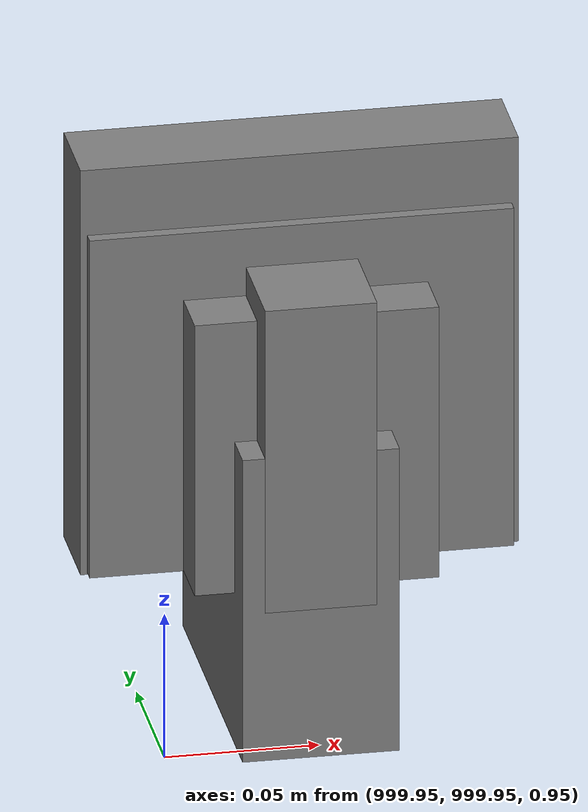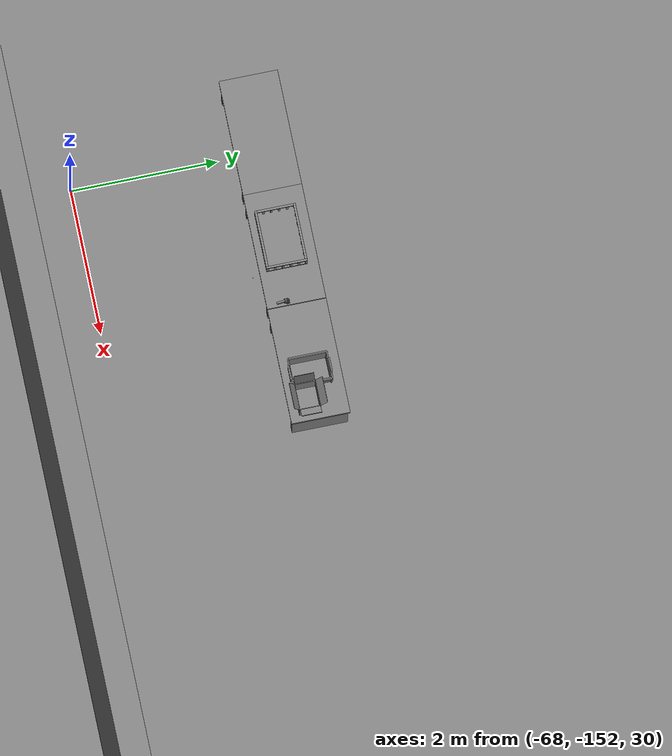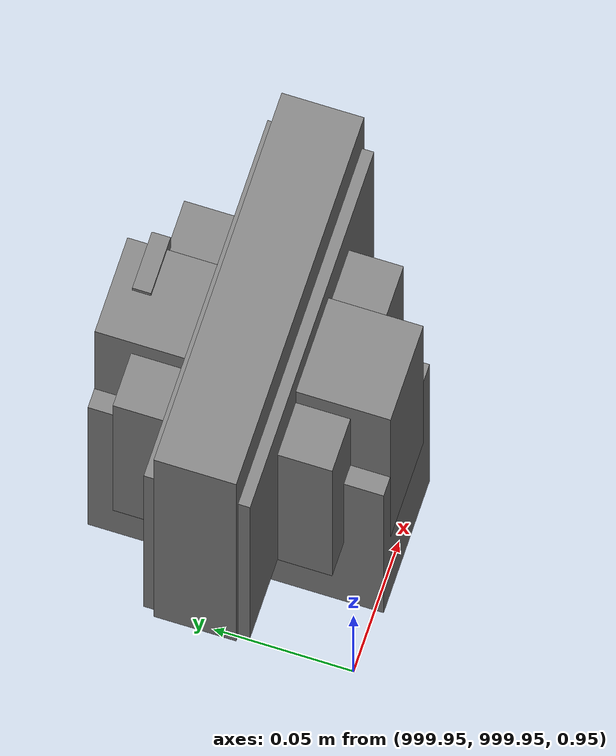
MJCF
<mujoco>
    <option gravity="0.000000000 0.000000000 -9.810000420" timestep="0.0049999999" integrator="implicitfast" density="1.225" viscosity="1.8000001e-05" noslip_iterations="10" iterations="100" sdf_iterations="50">
        <flag multiccd="disable"/>
    </option>
    <size memory="1000M"/>
    <compiler coordinate="local"/>
    <worldbody>
        <light cutoff="30" pos="0 1 1" dir="0 -1 -2"/>
        <light cutoff="30" pos="0 -1 1" dir="0 1 -2"/>
        <body pos="-64.866622925 -149.383972168 30.183746338" euler="89.999984741 89.999946594 0.000000000" name="openloong_gripper_2f85_fix_base_usda_bluebox_01">
            <geom contype="1" conaffinity="1" density="1000" type="box" material="" rgba="0.500000000 0.500000000 0.500000000 1.000000000" solimp="0.899999976 0.949999988 0.001000000" friction="1.000000000 0.005000000 0.000100000" solref="0.020000000 1.000000000" margin="0" condim="3" group="0" pos="0.276580811 0.187225342 0.000068665" quat="0.707106948 0.000077471 0.707106352 0.000077486" size="0.100000001 0.057999998 0.010000000" name="openloong_gripper_2f85_fix_base_usda_geom_126E4A71_ABEA_407F_85E4_41FC4869EE57"/>
            <geom contype="1" conaffinity="1" density="1000" type="box" material="" rgba="0.500000000 0.500000000 0.500000000 1.000000000" solimp="0.899999976 0.949999988 0.001000000" friction="1.000000000 0.005000000 0.000100000" solref="0.020000000 1.000000000" margin="0" condim="3" group="0" pos="0.000000000 0.002883911 0.000000000" quat="0.999999881 0.000000000 0.000000000 0.000000000" size="0.254000008 0.003000000 0.172000006" name="openloong_gripper_2f85_fix_base_usda_geom_BCC1F704_6C89_4218_8FAB_D62DB9D883B8"/>
            <geom contype="1" conaffinity="1" density="1000" type="box" material="" rgba="0.500000000 0.500000000 0.500000000 1.000000000" solimp="0.899999976 0.949999988 0.001000000" friction="1.000000000 0.005000000 0.000100000" solref="0.020000000 1.000000000" margin="0" condim="3" group="0" pos="0.000000000 0.124874115 0.173484802" quat="0.999796331 0.020176515 -0.000000015 0.000000030" size="0.259999990 0.119999997 0.007000000" name="openloong_gripper_2f85_fix_base_usda_geom_D8CC9C77_ACC8_4454_92FE_2A9D8C658365"/>
            <geom contype="1" conaffinity="1" density="1000" type="box" material="" rgba="0.500000000 0.500000000 0.500000000 1.000000000" solimp="0.899999976 0.949999988 0.001000000" friction="1.000000000 0.005000000 0.000100000" solref="0.020000000 1.000000000" margin="0" condim="3" group="0" pos="0.000000000 0.124874115 -0.173469543" quat="0.999796331 -0.020176545 -0.000000015 0.000000000" size="0.259999990 0.119999997 0.007000000" name="openloong_gripper_2f85_fix_base_usda_geom_8E53AB06_A420_4A0F_8BA7_DFAA8D79DEF2"/>
            <geom contype="1" conaffinity="1" density="1000" type="box" material="" rgba="0.500000000 0.500000000 0.500000000 1.000000000" solimp="0.899999976 0.949999988 0.001000000" friction="1.000000000 0.005000000 0.000100000" solref="0.020000000 1.000000000" margin="0" condim="3" group="0" pos="0.000000000 0.214008331 0.188980103" quat="0.999912977 0.013176724 0.000000015 0.000000000" size="0.259999990 0.029999999 0.012500000" name="openloong_gripper_2f85_fix_base_usda_geom_E236E9FC_B014_4C05_B839_1191DEA8F105"/>
            <geom contype="1" conaffinity="1" density="1000" type="box" material="" rgba="0.500000000 0.500000000 0.500000000 1.000000000" solimp="0.899999976 0.949999988 0.001000000" friction="1.000000000 0.005000000 0.000100000" solref="0.020000000 1.000000000" margin="0" condim="3" group="0" pos="-0.258361816 0.125289917 0.001876831" quat="0.702796936 -0.020792112 0.710783124 0.020769298" size="0.189999998 0.119999997 0.009000000" name="openloong_gripper_2f85_fix_base_usda_geom_DBCF905E_AF5F_48EC_953E_82BC93998336"/>
            <geom contype="1" conaffinity="1" density="1000" type="box" material="" rgba="0.500000000 0.500000000 0.500000000 1.000000000" solimp="0.899999976 0.949999988 0.001000000" friction="1.000000000 0.005000000 0.000100000" solref="0.020000000 1.000000000" margin="0" condim="3" group="0" pos="0.000000000 0.214008331 -0.188980103" quat="0.999912977 -0.013176769 0.000000030 0.000000015" size="0.259999990 0.029999999 0.012500000" name="openloong_gripper_2f85_fix_base_usda_geom_1FB7489E_A55F_42D6_9F50_A05D4E82D640"/>
            <geom contype="1" conaffinity="1" density="1000" type="box" material="" rgba="0.500000000 0.500000000 0.500000000 1.000000000" solimp="0.899999976 0.949999988 0.001000000" friction="1.000000000 0.005000000 0.000100000" solref="0.020000000 1.000000000" margin="0" condim="3" group="0" pos="-0.276611328 0.187225342 0.000068665" quat="0.707106650 0.000077441 0.707106709 0.000077456" size="0.100000001 0.057999998 0.010000000" name="openloong_gripper_2f85_fix_base_usda_geom_6B3494FA_0073_435C_A0DA_0A6AABEB534A"/>
            <geom contype="1" conaffinity="1" density="1000" type="box" material="" rgba="0.500000000 0.500000000 0.500000000 1.000000000" solimp="0.899999976 0.949999988 0.001000000" friction="1.000000000 0.005000000 0.000100000" solref="0.020000000 1.000000000" margin="0" condim="3" group="0" pos="0.258331299 0.125289917 0.001876831" quat="0.702851415 0.018856421 0.710823774 -0.019329369" size="0.189999998 0.119999997 0.009000000" name="openloong_gripper_2f85_fix_base_usda_geom_89C537F4_4BAF_4AC1_976B_22763A223D98"/>
            <freejoint name="openloong_gripper_2f85_fix_base_usda_bluebox_01_joint"/>
            <site size="0.005000000 0.005000000 0.005000000" rgba="0.500000000 0.500000000 0.500000000 1.000000000" pos="0.000000000 0.000000000 0.000000000" quat="0.999961913 0.008726534 0.000000000 0.000000000" group="0" type="sphere" name="openloong_gripper_2f85_fix_base_usda_bluebox_01site"/>
        </body>
        <body pos="-64.496299744 -149.491867065 30.235729218" euler="0.000000000 0.000000000 89.999946594" name="openloong_gripper_2f85_fix_base_usda_cardboardbox_01">
            <geom contype="1" conaffinity="1" density="1000" type="box" material="" rgba="0.500000000 0.500000000 0.500000000 1.000000000" solimp="0.899999976 0.949999988 0.001000000" friction="1.000000000 0.005000000 0.000100000" solref="0.020000000 1.000000000" margin="0" condim="3" group="0" pos="-0.003166199 -0.004086494 0.005052090" quat="1.000000000 0.000000000 0.000000000 0.000000000" size="0.142499998 0.177500010 0.005000000" name="openloong_gripper_2f85_fix_base_usda_geom_61E41B27_55C6_4A10_BF5E_71E9D952FF5C"/>
            <geom contype="1" conaffinity="1" density="1000" type="box" material="" rgba="0.500000000 0.500000000 0.500000000 1.000000000" solimp="0.899999976 0.949999988 0.001000000" friction="1.000000000 0.005000000 0.000100000" solref="0.020000000 1.000000000" margin="0" condim="3" group="0" pos="-0.003166199 0.170316696 0.150570869" quat="1.000000000 0.000000000 0.000000000 0.000000000" size="0.142499998 0.005000000 0.149999991" name="openloong_gripper_2f85_fix_base_usda_geom_7029B0F5_ABA2_42D7_A36A_EC8688489156"/>
            <geom contype="1" conaffinity="1" density="1000" type="box" material="" rgba="0.500000000 0.500000000 0.500000000 1.000000000" solimp="0.899999976 0.949999988 0.001000000" friction="1.000000000 0.005000000 0.000100000" solref="0.020000000 1.000000000" margin="0" condim="3" group="0" pos="-0.147399902 -0.005307198 0.150570869" quat="1.000000000 0.000000000 0.000000000 0.000000000" size="0.005000000 0.177500010 0.149999991" name="openloong_gripper_2f85_fix_base_usda_geom_D8DCEA6E_98EF_4D44_BBF3_D52F92E73355"/>
            <geom contype="1" conaffinity="1" density="1000" type="box" material="" rgba="0.500000000 0.500000000 0.500000000 1.000000000" solimp="0.899999976 0.949999988 0.001000000" friction="1.000000000 0.005000000 0.000100000" solref="0.020000000 1.000000000" margin="0" condim="3" group="0" pos="0.140275955 -0.005307198 0.150570869" quat="1.000000000 0.000000000 0.000000000 0.000000000" size="0.005000000 0.177500010 0.149999991" name="openloong_gripper_2f85_fix_base_usda_geom_83C89F72_AD6A_4338_9747_9518C2DC2BE3"/>
            <geom contype="1" conaffinity="1" density="1000" type="box" material="" rgba="0.500000000 0.500000000 0.500000000 1.000000000" solimp="0.899999976 0.949999988 0.001000000" friction="1.000000000 0.005000000 0.000100000" solref="0.020000000 1.000000000" margin="0" condim="3" group="0" pos="-0.003166199 -0.181550980 0.150570869" quat="1.000000000 0.000000000 0.000000000 0.000000000" size="0.142499998 0.005000000 0.149999991" name="openloong_gripper_2f85_fix_base_usda_geom_776D237A_FA4B_4F4C_B924_C6576CB068CE"/>
            <freejoint name="openloong_gripper_2f85_fix_base_usda_cardboardbox_01_joint"/>
            <site size="0.005000000 0.005000000 0.005000000" rgba="0.500000000 0.500000000 0.500000000 1.000000000" pos="0.000000000 0.000000000 0.000000000" quat="0.999961913 0.008726535 0.000000000 0.000000000" group="0" type="sphere" name="openloong_gripper_2f85_fix_base_usda_site_DE3AD9F0_F96C_4602_A373_03581602A6E5"/>
            <body pos="0.139160156 -0.004048347 0.301930904" euler="-179.999954224 49.383502960 179.999954224" name="openloong_gripper_2f85_fix_base_usda_A1_006">
                <geom contype="1" conaffinity="1" density="1000" type="box" material="" rgba="0.500000000 0.500000000 0.500000000 1.000000000" solimp="0.899999976 0.949999988 0.001000000" friction="1.000000000 0.005000000 0.000100000" solref="0.020000000 1.000000000" margin="0" condim="3" group="0" pos="-0.071587563 0.000009537 0.001745224" quat="0.999999881 0.000000000 0.000000000 0.000000000" size="0.071249999 0.179999992 0.002500000" name="openloong_gripper_2f85_fix_base_usda_geom_34799CBD_453B_4605_9718_D1285C67D1EC"/>
                <joint armature="0" stiffness="0.07" damping="0.0099999998" axis="0.000000 1.000000 0.000000" type="hinge" name="openloong_gripper_2f85_fix_base_usda_A1_006"/>
            </body>
            <body pos="-0.145902634 -0.004086494 0.301938057" euler="-180.000000000 -60.000011444 -180.000000000" name="openloong_gripper_2f85_fix_base_usda_A2_006">
                <geom contype="1" conaffinity="1" density="1000" type="box" material="" rgba="0.500000000 0.500000000 0.500000000 1.000000000" solimp="0.899999976 0.949999988 0.001000000" friction="1.000000000 0.005000000 0.000100000" solref="0.020000000 1.000000000" margin="0" condim="3" group="0" pos="0.071268082 0.000009537 0.002717972" quat="0.000002921 0.000000000 -0.000000030 0.999999881" size="0.071249999 0.179999992 0.002500000" name="openloong_gripper_2f85_fix_base_usda_geom_D0AFBD44_A9C2_4EEC_A35B_CB7A202739FF"/>
                <joint armature="0" stiffness="0.07" damping="0.0099999998" axis="0.000000 1.000000 0.000000" type="hinge" name="openloong_gripper_2f85_fix_base_usda_A2_006"/>
            </body>
            <body pos="-0.003385544 0.175991058 0.301930904" euler="-125.858116150 -0.000004561 0.000002331" name="openloong_gripper_2f85_fix_base_usda_B2_006">
                <geom contype="1" conaffinity="1" density="1000" type="box" material="" rgba="0.500000000 0.500000000 0.500000000 1.000000000" solimp="0.899999976 0.949999988 0.001000000" friction="1.000000000 0.005000000 0.000100000" solref="0.020000000 1.000000000" margin="0" condim="3" group="0" pos="0.000009537 -0.070939064 -0.002470016" quat="0.999614120 0.027776197 -0.000000015 0.000000030" size="0.137500003 0.064999998 0.005000000" name="openloong_gripper_2f85_fix_base_usda_geom_9A921C0E_9EEE_4BEA_B47E_47F33D303F47"/>
                <joint armature="0" stiffness="0.07" damping="0.0099999998" axis="1.000000 0.000000 0.000000" type="hinge" name="openloong_gripper_2f85_fix_base_usda_B2_006"/>
            </body>
            <body pos="-0.003385544 -0.184140205 0.301938057" euler="147.805557251 0.000000000 0.000000000" name="openloong_gripper_2f85_fix_base_usda_B1_006">
                <geom contype="1" conaffinity="1" density="1000" type="box" material="" rgba="0.500000000 0.500000000 0.500000000 1.000000000" solimp="0.899999976 0.949999988 0.001000000" friction="1.000000000 0.005000000 0.000100000" solref="0.020000000 1.000000000" margin="0" condim="3" group="0" pos="-0.000028610 0.070202351 -0.002703667" quat="0.999614179 -0.027776167 0.000000000 0.000000000" size="0.137500003 0.064999998 0.005000000" name="openloong_gripper_2f85_fix_base_usda_geom_1773E42A_8EFE_4CA7_982C_2061D63385C7"/>
                <joint armature="0" stiffness="0.07" damping="0.0099999998" axis="1.000000 0.000000 0.000000" type="hinge" name="openloong_gripper_2f85_fix_base_usda_B1_006"/>
            </body>
        </body>
        <body pos="-65.882858276 -149.481979370 30.229999542" euler="-64.487716675 0.000000000 0.000000000" name="openloong_gripper_2f85_fix_base_usda_Barcode">
            <geom contype="1" conaffinity="1" density="1000" type="box" material="" rgba="0.500000000 0.500000000 0.500000000 1.000000000" solimp="0.899999976 0.949999988 0.001000000" friction="1.000000000 0.005000000 0.000100000" solref="0.020000000 1.000000000" margin="0" condim="3" group="0" pos="0.000000000 0.013038635 0.001419067" quat="0.000000000 0.000000000 0.000000000 1.000000119" size="0.034000002 0.010000000 0.017999999" name="openloong_gripper_2f85_fix_base_usda_geom_0E0ACA94_3513_4D43_80EF_20F2D832DE8E"/>
            <geom contype="1" conaffinity="1" density="1000" type="box" material="" rgba="0.500000000 0.500000000 0.500000000 1.000000000" solimp="0.899999976 0.949999988 0.001000000" friction="1.000000000 0.005000000 0.000100000" solref="0.020000000 1.000000000" margin="0" condim="3" group="0" pos="0.000000000 -0.035301208 -0.007095337" quat="0.000000000 0.000000000 -0.043619365 0.999048233" size="0.028999999 0.010000000 0.020000000" name="openloong_gripper_2f85_fix_base_usda_geom_09E02FA1_2E8F_48FA_8A3C_21825AC01835"/>
            <geom contype="1" conaffinity="1" density="1000" type="box" material="" rgba="0.500000000 0.500000000 0.500000000 1.000000000" solimp="0.899999976 0.949999988 0.001000000" friction="1.000000000 0.005000000 0.000100000" solref="0.020000000 1.000000000" margin="0" condim="3" group="0" pos="0.000000000 -0.043411255 -0.011749268" quat="0.922262907 0.386563420 0.000000000 0.000000000" size="0.026000001 0.010000000 0.020000000" name="openloong_gripper_2f85_fix_base_usda_geom_E2FAB369_EBCD_48AD_8456_8E9DC46794E9"/>
            <geom contype="1" conaffinity="1" density="1000" type="box" material="" rgba="0.500000000 0.500000000 0.500000000 1.000000000" solimp="0.899999976 0.949999988 0.001000000" friction="1.000000000 0.005000000 0.000100000" solref="0.020000000 1.000000000" margin="0" condim="3" group="0" pos="0.000000000 -0.016967773 -0.031860352" quat="0.000000000 0.000000000 0.000000000 1.000000119" size="0.008000000 0.010000000 0.013000000" name="openloong_gripper_2f85_fix_base_usda_geom_D41F8BAC_73CA_47EA_AD9A_A3B71604C318"/>
            <geom contype="1" conaffinity="1" density="1000" type="box" material="" rgba="0.500000000 0.500000000 0.500000000 1.000000000" solimp="0.899999976 0.949999988 0.001000000" friction="1.000000000 0.005000000 0.000100000" solref="0.020000000 1.000000000" margin="0" condim="3" group="0" pos="0.000000000 -0.001869202 0.000312805" quat="0.953716993 0.300705761 0.000000000 0.000000000" size="0.032000002 0.010000000 0.018999999" name="openloong_gripper_2f85_fix_base_usda_geom_F8FB92F7_7406_4571_A217_343D4130D101"/>
            <geom contype="1" conaffinity="1" density="1000" type="box" material="" rgba="0.500000000 0.500000000 0.500000000 1.000000000" solimp="0.899999976 0.949999988 0.001000000" friction="1.000000000 0.005000000 0.000100000" solref="0.020000000 1.000000000" margin="0" condim="3" group="0" pos="0.000000000 -0.019531250 -0.003173828" quat="0.953716993 0.300705761 0.000000000 0.000000000" size="0.030999999 0.010000000 0.020000000" name="openloong_gripper_2f85_fix_base_usda_geom_316FB75B_5675_4102_8698_EF596AFD4D71"/>
            <geom contype="1" conaffinity="1" density="1000" type="box" material="" rgba="0.500000000 0.500000000 0.500000000 1.000000000" solimp="0.899999976 0.949999988 0.001000000" friction="1.000000000 0.005000000 0.000100000" solref="0.020000000 1.000000000" margin="0" condim="3" group="0" pos="0.000000000 -0.035301208 -0.007095337" quat="0.953716993 0.300705761 0.000000000 0.000000000" size="0.028999999 0.010000000 0.020000000" name="openloong_gripper_2f85_fix_base_usda_geom_7DCCCCA0_DFB6_487F_A240_A9F76ACD70FB"/>
            <geom contype="1" conaffinity="1" density="1000" type="box" material="" rgba="0.500000000 0.500000000 0.500000000 1.000000000" solimp="0.899999976 0.949999988 0.001000000" friction="1.000000000 0.005000000 0.000100000" solref="0.020000000 1.000000000" margin="0" condim="3" group="0" pos="0.000000000 -0.042617798 -0.071121216" quat="0.000000000 0.000000000 0.000000000 1.000000119" size="0.013000000 0.021000000 0.059999999" name="openloong_gripper_2f85_fix_base_usda_geom_17EE3656_083B_4488_B49F_D95EED6DFD87"/>
            <freejoint name="openloong_gripper_2f85_fix_base_usda_Barcode_joint"/>
            <site size="0.005000000 0.005000000 0.005000000" rgba="0.500000000 0.500000000 0.500000000 1.000000000" pos="0.000000000 0.000000000 0.000000000" quat="1.000000000 0.000000000 0.000000000 0.000000000" group="0" type="sphere" name="openloong_gripper_2f85_fix_base_usda_Barcode_site"/>
        </body>
        <body pos="-66.745018005 -149.392349243 30.184000015" euler="0.000000000 0.000000000 89.999946594" name="[22330348594558]_Basket_01">
            <geom contype="1" conaffinity="1" density="1000" type="box" material="" rgba="0.500000000 0.500000000 0.500000000 1.000000000" solimp="0.899999976 0.949999988 0.001000000" friction="1.000000000 0.005000000 0.000100000" solref="0.020000000 1.000000000" margin="0" condim="3" group="0" pos="-0.052425385 0.389207840 0.089787483" quat="0.707107008 0.000000000 0.000000000 0.707106411" size="0.014249999 0.014249999 0.059999999" name="[22330348594558]_geom_D3921633_B264_4831_B46D_371B1F034403"/>
            <geom contype="1" conaffinity="1" density="1000" type="box" material="" rgba="0.500000000 0.500000000 0.500000000 1.000000000" solimp="0.899999976 0.949999988 0.001000000" friction="1.000000000 0.005000000 0.000100000" solref="0.020000000 1.000000000" margin="0" condim="3" group="0" pos="0.264015198 -0.133043289 0.089787483" quat="0.707107008 0.000000000 0.000000000 0.707106411" size="0.014249999 0.014249999 0.059999999" name="[22330348594558]_geom_05748C90_F03B_4D9B_9A4E_1970EA036C02"/>
            <geom contype="1" conaffinity="1" density="1000" type="box" material="" rgba="0.500000000 0.500000000 0.500000000 1.000000000" solimp="0.899999976 0.949999988 0.001000000" friction="1.000000000 0.005000000 0.000100000" solref="0.020000000 1.000000000" margin="0" condim="3" group="0" pos="-0.264015198 -0.265548706 0.089793205" quat="0.707107008 0.000000000 0.000000000 0.707106411" size="0.014249999 0.014249999 0.059999999" name="[22330348594558]_geom_63BBB592_5D04_4769_835C_8E31FCF94F7D"/>
            <geom contype="1" conaffinity="1" density="1000" type="box" material="" rgba="0.500000000 0.500000000 0.500000000 1.000000000" solimp="0.899999976 0.949999988 0.001000000" friction="1.000000000 0.005000000 0.000100000" solref="0.020000000 1.000000000" margin="0" condim="3" group="0" pos="-0.160263062 -0.389322281 0.089793205" quat="0.707107008 0.000000000 0.000000000 0.707106411" size="0.014249999 0.014249999 0.059999999" name="[22330348594558]_geom_A95190F8_54B9_4ED5_96E7_50A74AF12BDE"/>
            <geom contype="1" conaffinity="1" density="1000" type="box" material="" rgba="0.500000000 0.500000000 0.500000000 1.000000000" solimp="0.899999976 0.949999988 0.001000000" friction="1.000000000 0.005000000 0.000100000" solref="0.020000000 1.000000000" margin="0" condim="3" group="0" pos="0.162265778 -0.389322281 0.089787483" quat="0.707107008 0.000000000 0.000000000 0.707106411" size="0.014249999 0.014249999 0.059999999" name="[22330348594558]_geom_143115B6_1499_4130_A196_CD4CCCC8BC23"/>
            <geom contype="1" conaffinity="1" density="1000" type="box" material="" rgba="0.500000000 0.500000000 0.500000000 1.000000000" solimp="0.899999976 0.949999988 0.001000000" friction="1.000000000 0.005000000 0.000100000" solref="0.020000000 1.000000000" margin="0" condim="3" group="0" pos="0.264015198 0.389207840 0.089787483" quat="0.707107008 0.000000000 0.000000000 0.707106411" size="0.014249999 0.014249999 0.059999999" name="[22330348594558]_geom_A0E99A43_0AC5_4AF9_9C5F_5FC031AD6CA1"/>
            <geom contype="1" conaffinity="1" density="1000" type="box" material="" rgba="0.500000000 0.500000000 0.500000000 1.000000000" solimp="0.899999976 0.949999988 0.001000000" friction="1.000000000 0.005000000 0.000100000" solref="0.020000000 1.000000000" margin="0" condim="3" group="0" pos="-0.264015198 -0.133043289 0.089793205" quat="0.707107008 0.000000000 0.000000000 0.707106411" size="0.014249999 0.014249999 0.059999999" name="[22330348594558]_geom_9B6F5408_362E_4B91_B142_C618A36F0171"/>
            <geom contype="1" conaffinity="1" density="1000" type="box" material="" rgba="0.500000000 0.500000000 0.500000000 1.000000000" solimp="0.899999976 0.949999988 0.001000000" friction="1.000000000 0.005000000 0.000100000" solref="0.020000000 1.000000000" margin="0" condim="3" group="0" pos="-0.264026642 0.269256592 0.089793205" quat="0.707107008 0.000000000 0.000000000 0.707106411" size="0.014249999 0.014249999 0.059999999" name="[22330348594558]_geom_968D0807_FE96_4EA6_AFCE_FAF01B3C032D"/>
            <geom contype="1" conaffinity="1" density="1000" type="box" material="" rgba="0.500000000 0.500000000 0.500000000 1.000000000" solimp="0.899999976 0.949999988 0.001000000" friction="1.000000000 0.005000000 0.000100000" solref="0.020000000 1.000000000" margin="0" condim="3" group="0" pos="0.054462433 0.389207840 0.089787483" quat="0.707107008 0.000000000 0.000000000 0.707106411" size="0.014249999 0.014249999 0.059999999" name="[22330348594558]_geom_4463C44E_6A00_4E84_87FA_B8D259C1C3EF"/>
            <geom contype="1" conaffinity="1" density="1000" type="box" material="" rgba="0.500000000 0.500000000 0.500000000 1.000000000" solimp="0.899999976 0.949999988 0.001000000" friction="1.000000000 0.005000000 0.000100000" solref="0.020000000 1.000000000" margin="0" condim="3" group="0" pos="0.054462433 -0.389322281 0.089787483" quat="0.707107008 0.000000000 0.000000000 0.707106411" size="0.014249999 0.014249999 0.059999999" name="[22330348594558]_geom_25DB30D4_CF18_4215_8391_51F1009B4A28"/>
            <geom contype="1" conaffinity="1" density="1000" type="box" material="" rgba="0.500000000 0.500000000 0.500000000 1.000000000" solimp="0.899999976 0.949999988 0.001000000" friction="1.000000000 0.005000000 0.000100000" solref="0.020000000 1.000000000" margin="0" condim="3" group="0" pos="0.264015198 0.269256592 0.089793205" quat="0.707107008 0.000000000 0.000000000 0.707106411" size="0.014249999 0.014249999 0.059999999" name="[22330348594558]_geom_00983D04_4C71_41BB_9EA2_A984C61148C0"/>
            <geom contype="1" conaffinity="1" density="1000" type="box" material="" rgba="0.500000000 0.500000000 0.500000000 1.000000000" solimp="0.899999976 0.949999988 0.001000000" friction="1.000000000 0.005000000 0.000100000" solref="0.020000000 1.000000000" margin="0" condim="3" group="0" pos="0.264015198 -0.389322281 0.089787483" quat="0.707107008 0.000000000 0.000000000 0.707106411" size="0.014249999 0.014249999 0.059999999" name="[22330348594558]_geom_2A75271C_8894_4643_B4FE_D97BABD65E5B"/>
            <geom contype="1" conaffinity="1" density="1000" type="box" material="" rgba="0.500000000 0.500000000 0.500000000 1.000000000" solimp="0.899999976 0.949999988 0.001000000" friction="1.000000000 0.005000000 0.000100000" solref="0.020000000 1.000000000" margin="0" condim="3" group="0" pos="0.000000000 0.000000000 0.015998840" quat="0.707107008 0.000000000 0.000000000 0.707106411" size="0.403499991 0.279000014 0.015750000" name="[22330348594558]_geom_2409C838_31E6_4544_90D9_46A185BEA7B1"/>
            <geom contype="1" conaffinity="1" density="1000" type="box" material="" rgba="0.500000000 0.500000000 0.500000000 1.000000000" solimp="0.899999976 0.949999988 0.001000000" friction="1.000000000 0.005000000 0.000100000" solref="0.020000000 1.000000000" margin="0" condim="3" group="0" pos="0.000000000 -0.389476776 0.163619041" quat="0.707107008 0.000000000 0.000000000 0.707106411" size="0.015000000 0.277500004 0.015750000" name="[22330348594558]_geom_9B91A8B1_5920_4871_9927_A5DF2423653C"/>
            <geom contype="1" conaffinity="1" density="1000" type="box" material="" rgba="0.500000000 0.500000000 0.500000000 1.000000000" solimp="0.899999976 0.949999988 0.001000000" friction="1.000000000 0.005000000 0.000100000" solref="0.020000000 1.000000000" margin="0" condim="3" group="0" pos="0.162265778 0.389207840 0.089787483" quat="0.707107008 0.000000000 0.000000000 0.707106411" size="0.014249999 0.014249999 0.059999999" name="[22330348594558]_geom_F98275CE_BEB0_4FD8_BF77_B847757BC9F0"/>
            <geom contype="1" conaffinity="1" density="1000" type="box" material="" rgba="0.500000000 0.500000000 0.500000000 1.000000000" solimp="0.899999976 0.949999988 0.001000000" friction="1.000000000 0.005000000 0.000100000" solref="0.020000000 1.000000000" margin="0" condim="3" group="0" pos="0.000000000 0.389471054 0.163619041" quat="0.707107008 0.000000000 0.000000000 0.707106411" size="0.015000000 0.277500004 0.015750000" name="[22330348594558]_geom_B70D879E_485E_4C7C_A33F_F67628489005"/>
            <geom contype="1" conaffinity="1" density="1000" type="box" material="" rgba="0.500000000 0.500000000 0.500000000 1.000000000" solimp="0.899999976 0.949999988 0.001000000" friction="1.000000000 0.005000000 0.000100000" solref="0.020000000 1.000000000" margin="0" condim="3" group="0" pos="-0.263511658 0.000000000 0.163619041" quat="0.707107008 0.000000000 0.000000000 0.707106411" size="0.403499991 0.015000000 0.015750000" name="[22330348594558]_geom_9362B71D_1188_4FD3_8B4A_F113D6359710"/>
            <geom contype="1" conaffinity="1" density="1000" type="box" material="" rgba="0.500000000 0.500000000 0.500000000 1.000000000" solimp="0.899999976 0.949999988 0.001000000" friction="1.000000000 0.005000000 0.000100000" solref="0.020000000 1.000000000" margin="0" condim="3" group="0" pos="-0.264015198 0.141334534 0.089793205" quat="0.707107008 0.000000000 0.000000000 0.707106411" size="0.014249999 0.014249999 0.059999999" name="[22330348594558]_geom_1CD95229_56BF_48A9_A21D_966D37B8F11A"/>
            <geom contype="1" conaffinity="1" density="1000" type="box" material="" rgba="0.500000000 0.500000000 0.500000000 1.000000000" solimp="0.899999976 0.949999988 0.001000000" friction="1.000000000 0.005000000 0.000100000" solref="0.020000000 1.000000000" margin="0" condim="3" group="0" pos="0.264015198 -0.265548706 0.089787483" quat="0.707107008 0.000000000 0.000000000 0.707106411" size="0.014249999 0.014249999 0.059999999" name="[22330348594558]_geom_FE1E0665_01EA_441E_B4BE_BCB7F8FF3801"/>
            <geom contype="1" conaffinity="1" density="1000" type="box" material="" rgba="0.500000000 0.500000000 0.500000000 1.000000000" solimp="0.899999976 0.949999988 0.001000000" friction="1.000000000 0.005000000 0.000100000" solref="0.020000000 1.000000000" margin="0" condim="3" group="0" pos="-0.160263062 0.389207840 0.089787483" quat="0.707107008 0.000000000 0.000000000 0.707106411" size="0.014249999 0.014249999 0.059999999" name="[22330348594558]_geom_74168371_9BD8_4298_888B_704EE835714A"/>
            <geom contype="1" conaffinity="1" density="1000" type="box" material="" rgba="0.500000000 0.500000000 0.500000000 1.000000000" solimp="0.899999976 0.949999988 0.001000000" friction="1.000000000 0.005000000 0.000100000" solref="0.020000000 1.000000000" margin="0" condim="3" group="0" pos="-0.052425385 -0.389322281 0.089787483" quat="0.707107008 0.000000000 0.000000000 0.707106411" size="0.014249999 0.014249999 0.059999999" name="[22330348594558]_geom_0E89707C_AE17_42C9_AC01_921932DBD30C"/>
            <geom contype="1" conaffinity="1" density="1000" type="box" material="" rgba="0.500000000 0.500000000 0.500000000 1.000000000" solimp="0.899999976 0.949999988 0.001000000" friction="1.000000000 0.005000000 0.000100000" solref="0.020000000 1.000000000" margin="0" condim="3" group="0" pos="-0.264026642 -0.389322281 0.089793205" quat="0.707107008 0.000000000 0.000000000 0.707106411" size="0.014249999 0.014249999 0.059999999" name="[22330348594558]_geom_3189AD92_2B82_4A91_8B7F_D4FA5E383E0D"/>
            <geom contype="1" conaffinity="1" density="1000" type="box" material="" rgba="0.500000000 0.500000000 0.500000000 1.000000000" solimp="0.899999976 0.949999988 0.001000000" friction="1.000000000 0.005000000 0.000100000" solref="0.020000000 1.000000000" margin="0" condim="3" group="0" pos="0.264015198 0.141334534 0.089787483" quat="0.707107008 0.000000000 0.000000000 0.707106411" size="0.014249999 0.014249999 0.059999999" name="[22330348594558]_geom_47B72928_099E_4350_B953_72E8A943F4BB"/>
            <geom contype="1" conaffinity="1" density="1000" type="box" material="" rgba="0.500000000 0.500000000 0.500000000 1.000000000" solimp="0.899999976 0.949999988 0.001000000" friction="1.000000000 0.005000000 0.000100000" solref="0.020000000 1.000000000" margin="0" condim="3" group="0" pos="-0.264015198 0.389207840 0.089793205" quat="0.707107008 0.000000000 0.000000000 0.707106411" size="0.014249999 0.014249999 0.059999999" name="[22330348594558]_geom_3EC7313D_9BF0_47B2_933F_2D2C1FF79E3B"/>
            <geom contype="1" conaffinity="1" density="1000" type="box" material="" rgba="0.500000000 0.500000000 0.500000000 1.000000000" solimp="0.899999976 0.949999988 0.001000000" friction="1.000000000 0.005000000 0.000100000" solref="0.020000000 1.000000000" margin="0" condim="3" group="0" pos="0.264015198 0.004480362 0.089787483" quat="0.707107008 0.000000000 0.000000000 0.707106411" size="0.014249999 0.014249999 0.059999999" name="[22330348594558]_geom_DA45B179_4EE2_400E_8B81_28CF1729BA5F"/>
            <geom contype="1" conaffinity="1" density="1000" type="box" material="" rgba="0.500000000 0.500000000 0.500000000 1.000000000" solimp="0.899999976 0.949999988 0.001000000" friction="1.000000000 0.005000000 0.000100000" solref="0.020000000 1.000000000" margin="0" condim="3" group="0" pos="0.263694763 -0.000011444 0.163619041" quat="0.707107008 0.000000000 0.000000000 0.707106411" size="0.403499991 0.015000000 0.015750000" name="[22330348594558]_geom_93DAA93F_F631_421B_8705_27FED1125D66"/>
            <geom contype="1" conaffinity="1" density="1000" type="box" material="" rgba="0.500000000 0.500000000 0.500000000 1.000000000" solimp="0.899999976 0.949999988 0.001000000" friction="1.000000000 0.005000000 0.000100000" solref="0.020000000 1.000000000" margin="0" condim="3" group="0" pos="-0.264015198 0.004480362 0.089793205" quat="0.707107008 0.000000000 0.000000000 0.707106411" size="0.014249999 0.014249999 0.059999999" name="[22330348594558]_geom_244274E4_737E_4654_8FB0_8AF6755377FD"/>
            <freejoint name="[22330348594558]_joint_F5BE0A9B_B2C7_435B_90C8_6F4B442C6D85"/>
        </body>
        <body pos="0.000000000 0.000000000 0.000000000" euler="0.000000000 0.000000000 0.000000000" name="Static Objects_Static Objects">
            <geom contype="1" conaffinity="1" density="1000" type="box" material="" rgba="0.500000000 0.500000000 0.500000000 1.000000000" solimp="0.899999976 0.949999988 0.001000000" friction="1.000000000 0.005000000 0.000100000" solref="0.020000000 1.000000000" margin="0" condim="3" group="0" pos="-67.544113159 -149.365814209 29.727830887" quat="0.500000417 0.499999970 0.499999553 0.499999970" size="0.381000012 0.319999993 0.041000001" name="Static Objects_geom_FE03D62E_153C_4122_8EA3_523D1F1BBFB0"/>
            <geom contype="1" conaffinity="1" density="1000" type="box" material="" rgba="0.500000000 0.500000000 0.500000000 1.000000000" solimp="0.899999976 0.949999988 0.001000000" friction="1.000000000 0.005000000 0.000100000" solref="0.020000000 1.000000000" margin="0" condim="3" group="0" pos="-68.239501953 -149.365814209 30.086868286" quat="0.500000417 0.499999970 0.499999553 0.499999970" size="0.370999992 0.039500002 0.745000005" name="Static Objects_geom_03C16B5C_C594_4BB2_93B0_230823A6C069"/>
            <geom contype="1" conaffinity="1" density="1000" type="box" material="" rgba="0.500000000 0.500000000 0.500000000 1.000000000" solimp="0.899999976 0.949999988 0.001000000" friction="1.000000000 0.005000000 0.000100000" solref="0.020000000 1.000000000" margin="0" condim="3" group="0" pos="-68.239501953 -149.365814209 30.147235870" quat="0.500000417 0.499999970 0.499999553 0.499999970" size="0.400000006 0.022000000 0.800000012" name="Static Objects_geom_34719652_D6C1_42C8_AF3D_CBDBC05F3842"/>
            <geom contype="1" conaffinity="1" density="1000" type="box" material="" rgba="0.500000000 0.500000000 0.500000000 1.000000000" solimp="0.899999976 0.949999988 0.001000000" friction="1.000000000 0.005000000 0.000100000" solref="0.020000000 1.000000000" margin="0" condim="3" group="0" pos="-68.934890747 -149.365814209 29.727830887" quat="0.500000417 0.499999970 0.499999553 0.499999970" size="0.381000012 0.319999993 0.041000001" name="Static Objects_geom_43B8029A_3F61_4CC4_B66A_23EACA8B3499"/>
            <geom contype="1" conaffinity="1" density="1000" type="box" material="" rgba="0.500000000 0.500000000 0.500000000 1.000000000" solimp="0.899999976 0.949999988 0.001000000" friction="1.000000000 0.005000000 0.000100000" solref="0.020000000 1.000000000" margin="0" condim="3" group="0" pos="-68.239501953 -149.365814209 29.561563492" quat="0.500000417 0.499999970 0.499999553 0.499999970" size="0.020000000 0.022000000 0.660000026" name="Static Objects_geom_A01EBF6A_9675_442F_B758_94219C498441"/>
            <geom contype="1" conaffinity="1" density="1000" type="box" material="" rgba="0.500000000 0.500000000 0.500000000 1.000000000" solimp="0.899999976 0.949999988 0.001000000" friction="1.000000000 0.005000000 0.000100000" solref="0.020000000 1.000000000" margin="0" condim="3" group="0" pos="-65.945671082 -149.365814209 29.727830887" quat="0.500000417 0.499999970 0.499999553 0.499999970" size="0.381000012 0.319999993 0.041000001" name="Static Objects_geom_E31FB8C9_DB7B_40BF_9F2F_548B36B869E1"/>
            <geom contype="1" conaffinity="1" density="1000" type="box" material="" rgba="0.500000000 0.500000000 0.500000000 1.000000000" solimp="0.899999976 0.949999988 0.001000000" friction="1.000000000 0.005000000 0.000100000" solref="0.020000000 1.000000000" margin="0" condim="3" group="0" pos="-66.641059875 -149.365814209 30.086868286" quat="0.500000417 0.499999970 0.499999553 0.499999970" size="0.370999992 0.039500002 0.745000005" name="Static Objects_geom_83A02A04_9914_4EF8_A38A_A22F3E1ED9AB"/>
            <geom contype="1" conaffinity="1" density="1000" type="box" material="" rgba="0.500000000 0.500000000 0.500000000 1.000000000" solimp="0.899999976 0.949999988 0.001000000" friction="1.000000000 0.005000000 0.000100000" solref="0.020000000 1.000000000" margin="0" condim="3" group="0" pos="-66.641059875 -149.365814209 30.147235870" quat="0.500000417 0.499999970 0.499999553 0.499999970" size="0.400000006 0.022000000 0.800000012" name="Static Objects_geom_6425BF82_0912_4B6C_9F5E_C30F38453366"/>
            <geom contype="1" conaffinity="1" density="1000" type="box" material="" rgba="0.500000000 0.500000000 0.500000000 1.000000000" solimp="0.899999976 0.949999988 0.001000000" friction="1.000000000 0.005000000 0.000100000" solref="0.020000000 1.000000000" margin="0" condim="3" group="0" pos="-67.336448669 -149.365814209 29.727830887" quat="0.500000417 0.499999970 0.499999553 0.499999970" size="0.381000012 0.319999993 0.041000001" name="Static Objects_geom_0ED3CCFE_511E_4EFA_AB8A_C23B45F89419"/>
            <geom contype="1" conaffinity="1" density="1000" type="box" material="" rgba="0.500000000 0.500000000 0.500000000 1.000000000" solimp="0.899999976 0.949999988 0.001000000" friction="1.000000000 0.005000000 0.000100000" solref="0.020000000 1.000000000" margin="0" condim="3" group="0" pos="-66.641059875 -149.365814209 29.561563492" quat="0.500000417 0.499999970 0.499999553 0.499999970" size="0.020000000 0.022000000 0.660000026" name="Static Objects_geom_2336FACE_5C12_4E7B_AED2_163D0084D3F9"/>
            <geom contype="1" conaffinity="1" density="1000" type="box" material="" rgba="0.500000000 0.500000000 0.500000000 1.000000000" solimp="0.899999976 0.949999988 0.001000000" friction="1.000000000 0.005000000 0.000100000" solref="0.020000000 1.000000000" margin="0" condim="3" group="0" pos="-64.338577271 -149.365814209 29.727830887" quat="0.500000417 0.499999970 0.499999553 0.499999970" size="0.381000012 0.319999993 0.041000001" name="Static Objects_geom_D58D5623_4FB0_43CE_BF18_2D21E3C4319E"/>
            <geom contype="1" conaffinity="1" density="1000" type="box" material="" rgba="0.500000000 0.500000000 0.500000000 1.000000000" solimp="0.899999976 0.949999988 0.001000000" friction="1.000000000 0.005000000 0.000100000" solref="0.020000000 1.000000000" margin="0" condim="3" group="0" pos="-65.033966064 -149.365814209 30.086868286" quat="0.500000417 0.499999970 0.499999553 0.499999970" size="0.370999992 0.039500002 0.745000005" name="Static Objects_geom_153FCAB1_0556_46D1_B168_B1A9C3F3F904"/>
            <geom contype="1" conaffinity="1" density="1000" type="box" material="" rgba="0.500000000 0.500000000 0.500000000 1.000000000" solimp="0.899999976 0.949999988 0.001000000" friction="1.000000000 0.005000000 0.000100000" solref="0.020000000 1.000000000" margin="0" condim="3" group="0" pos="-65.033966064 -149.365814209 30.147235870" quat="0.500000417 0.499999970 0.499999553 0.499999970" size="0.400000006 0.022000000 0.800000012" name="Static Objects_geom_EA309BD8_252D_4126_AE7E_84BC674275C1"/>
            <geom contype="1" conaffinity="1" density="1000" type="box" material="" rgba="0.500000000 0.500000000 0.500000000 1.000000000" solimp="0.899999976 0.949999988 0.001000000" friction="1.000000000 0.005000000 0.000100000" solref="0.020000000 1.000000000" margin="0" condim="3" group="0" pos="-65.729354858 -149.365814209 29.727830887" quat="0.500000417 0.499999970 0.499999553 0.499999970" size="0.381000012 0.319999993 0.041000001" name="Static Objects_geom_84C68AD6_1DA4_44AB_A24B_256902016F0E"/>
            <geom contype="1" conaffinity="1" density="1000" type="box" material="" rgba="0.500000000 0.500000000 0.500000000 1.000000000" solimp="0.899999976 0.949999988 0.001000000" friction="1.000000000 0.005000000 0.000100000" solref="0.020000000 1.000000000" margin="0" condim="3" group="0" pos="-65.033966064 -149.365814209 29.561563492" quat="0.500000417 0.499999970 0.499999553 0.499999970" size="0.020000000 0.022000000 0.660000026" name="Static Objects_geom_ABD04117_B7DF_46C1_B827_26CD4E21BE73"/>
            <geom contype="1" conaffinity="1" density="1000" type="box" material="" rgba="0.500000000 0.500000000 0.500000000 1.000000000" solimp="0.899999976 0.949999988 0.001000000" friction="1.000000000 0.005000000 0.000100000" solref="0.020000000 1.000000000" margin="0" condim="3" group="0" pos="-61.754566193 -137.853729248 33.906845093" quat="0.707107067 0.000000000 0.000000000 0.707106471" size="0.759999990 0.759999990 4.500000000" name="Static Objects_geom_BDDC9140_E4C3_4B7F_B9B9_9D8BF111FC4F"/>
            <geom contype="1" conaffinity="1" density="1000" type="box" material="" rgba="0.500000000 0.500000000 0.500000000 1.000000000" solimp="0.899999976 0.949999988 0.001000000" friction="1.000000000 0.005000000 0.000100000" solref="0.020000000 1.000000000" margin="0" condim="3" group="0" pos="-57.511135101 -144.927108765 31.707921982" quat="1.000000000 0.000000000 0.000000000 0.000000000" size="0.200000003 8.000000000 2.299999952" name="Static Objects_geom_97553C86_51B7_47EB_834E_157D3ABB176E"/>
            <geom contype="1" conaffinity="1" density="1000" type="box" material="" rgba="0.500000000 0.500000000 0.500000000 1.000000000" solimp="0.899999976 0.949999988 0.001000000" friction="1.000000000 0.005000000 0.000100000" solref="0.020000000 1.000000000" margin="0" condim="3" group="0" pos="-80.517646790 -157.574050903 31.688196182" quat="0.707107067 0.000000000 0.000000000 0.707106471" size="0.600000024 0.600000024 2.299999952" name="Static Objects_geom_936E8D5B_ABF2_409D_9E14_3C1A2450E396"/>
            <geom contype="1" conaffinity="1" density="1000" type="box" material="" rgba="0.500000000 0.500000000 0.500000000 1.000000000" solimp="0.899999976 0.949999988 0.001000000" friction="1.000000000 0.005000000 0.000100000" solref="0.020000000 1.000000000" margin="0" condim="3" group="0" pos="-80.711044312 -147.414932251 31.666158676" quat="1.000000000 0.000000000 0.000000000 0.000000000" size="0.200000003 10.000000000 2.299999952" name="Static Objects_geom_715921B1_61EE_405A_94FC_191D5A1653E6"/>
            <geom contype="1" conaffinity="1" density="1000" type="box" material="" rgba="0.500000000 0.500000000 0.500000000 1.000000000" solimp="0.899999976 0.949999988 0.001000000" friction="1.000000000 0.005000000 0.000100000" solref="0.020000000 1.000000000" margin="0" condim="3" group="0" pos="-57.687217712 -137.434692383 31.688196182" quat="0.707107067 0.000000000 0.000000000 0.707106471" size="0.600000024 0.600000024 2.299999952" name="Static Objects_geom_A73B87E4_7963_4311_B263_64D3E5AEA0E2"/>
            <geom contype="1" conaffinity="1" density="1000" type="box" material="" rgba="0.500000000 0.500000000 0.500000000 1.000000000" solimp="0.899999976 0.949999988 0.001000000" friction="1.000000000 0.005000000 0.000100000" solref="0.020000000 1.000000000" margin="0" condim="3" group="0" pos="-69.537033081 -140.263229370 31.714921951" quat="0.707107067 0.000000000 0.000000000 0.707106471" size="0.759999990 4.500000000 2.299999952" name="Static Objects_geom_DF4A707A_286E_46BD_9A71_95AA0A1E2F93"/>
            <geom contype="1" conaffinity="1" density="1000" type="box" material="" rgba="0.500000000 0.500000000 0.500000000 1.000000000" solimp="0.899999976 0.949999988 0.001000000" friction="1.000000000 0.005000000 0.000100000" solref="0.020000000 1.000000000" margin="0" condim="3" group="0" pos="-80.073638916 -137.853713989 33.906845093" quat="0.707107067 0.000000000 0.000000000 0.707106471" size="0.759999990 0.759999990 4.500000000" name="Static Objects_geom_94DEFA32_FA7A_48D8_9600_DDCC3AE2B00C"/>
            <geom contype="1" conaffinity="1" density="1000" type="box" material="" rgba="0.500000000 0.500000000 0.500000000 1.000000000" solimp="0.899999976 0.949999988 0.001000000" friction="1.000000000 0.005000000 0.000100000" solref="0.020000000 1.000000000" margin="0" condim="3" group="0" pos="-73.406707764 -155.734664917 31.707921982" quat="1.000000000 0.000000000 0.000000000 0.000000000" size="0.200000003 3.000000000 2.299999952" name="Static Objects_geom_023BEE8C_7969_4C06_92BC_37227A101364"/>
            <geom contype="1" conaffinity="1" density="1000" type="box" material="" rgba="0.500000000 0.500000000 0.500000000 1.000000000" solimp="0.899999976 0.949999988 0.001000000" friction="1.000000000 0.005000000 0.000100000" solref="0.020000000 1.000000000" margin="0" condim="3" group="0" pos="-68.497543335 -137.448257446 31.707921982" quat="0.707107067 0.000000000 0.000000000 0.707106471" size="0.200000003 14.000000000 2.299999952" name="Static Objects_geom_B3084EFD_1A06_45FA_AF9E_74907DFD177D"/>
            <geom contype="1" conaffinity="1" density="1000" type="cylinder" material="" rgba="0.500000000 0.500000000 0.500000000 1.000000000" solimp="0.899999976 0.949999988 0.001000000" friction="1.000000000 0.005000000 0.000100000" solref="0.020000000 1.000000000" margin="0" condim="3" group="0" pos="-68.868522644 -142.134506226 31.711090088" quat="0.707107067 0.000000000 0.000000000 0.707106471" size="0.509999990 2.299999952 1.000000000" name="Static Objects_geom_702DBFBF_DDB3_4641_9305_8749ACCF0D36"/>
            <geom contype="1" conaffinity="1" density="1000" type="plane" material="" rgba="0.500000000 0.500000000 0.500000000 1.000000000" solimp="0.899999976 0.949999988 0.001000000" friction="1.000000000 0.005000000 0.000100000" solref="0.020000000 1.000000000" margin="0" condim="3" group="0" pos="-72.873703003 -147.131927490 29.409669876" quat="1.000000000 0.000000000 0.000000000 0.000000000" size="18.000000000 14.000000000 1.000000000" name="Static Objects_geom_E1822E58_DD2E_421C_9A93_E117F8298A74"/>
            <geom contype="1" conaffinity="1" density="1000" type="box" material="" rgba="0.500000000 0.500000000 0.500000000 1.000000000" solimp="0.899999976 0.949999988 0.001000000" friction="1.000000000 0.005000000 0.000100000" solref="0.020000000 1.000000000" margin="0" condim="3" group="0" pos="-79.943580627 -157.782272339 31.707921982" quat="0.707107067 0.000000000 0.000000000 0.707106471" size="0.200000003 7.000000000 2.299999952" name="Static Objects_geom_606FDA5C_6752_4D7A_A82D_0654DCC1DB06"/>
            <geom contype="1" conaffinity="1" density="1000" type="box" material="" rgba="0.500000000 0.500000000 0.500000000 1.000000000" solimp="0.899999976 0.949999988 0.001000000" friction="1.000000000 0.005000000 0.000100000" solref="0.020000000 1.000000000" margin="0" condim="3" group="0" pos="-65.421028137 -152.903442383 31.707921982" quat="0.707107067 0.000000000 0.000000000 0.707106471" size="0.200000003 7.800000191 2.299999952" name="Static Objects_geom_F5F02DE0_680B_46BF_A48A_3458747B8C20"/>
            <geom contype="1" conaffinity="1" density="1000" type="box" material="" rgba="0.500000000 0.500000000 0.500000000 1.000000000" solimp="0.899999976 0.949999988 0.001000000" friction="1.000000000 0.005000000 0.000100000" solref="0.020000000 1.000000000" margin="0" condim="3" group="0" pos="-74.776908875 -149.964416504 31.688196182" quat="1.000000000 0.000000000 0.000000000 0.000000000" size="0.600000024 0.409999996 2.299999952" name="Static Objects_geom_D29B2BD4_A877_44FE_934C_6C218D9A778C"/>
            <geom contype="1" conaffinity="1" density="1000" type="cylinder" material="" rgba="0.500000000 0.500000000 0.500000000 1.000000000" solimp="0.899999976 0.949999988 0.001000000" friction="1.000000000 0.005000000 0.000100000" solref="0.020000000 1.000000000" margin="0" condim="3" group="0" pos="-60.161884308 -142.134506226 31.711090088" quat="0.707107067 0.000000000 0.000000000 0.707106471" size="0.509999990 2.299999952 1.000000000" name="Static Objects_geom_4E18C212_9B7A_48AF_B246_EA2955457C2E"/>
            <geom contype="1" conaffinity="1" density="1000" type="cylinder" material="" rgba="0.500000000 0.500000000 0.500000000 1.000000000" solimp="0.899999976 0.949999988 0.001000000" friction="1.000000000 0.005000000 0.000100000" solref="0.020000000 1.000000000" margin="0" condim="3" group="0" pos="-75.382453918 -149.963455200 31.711090088" quat="0.707107067 0.000000000 0.000000000 0.707106471" size="0.409999996 2.299999952 1.000000000" name="Static Objects_geom_A0F11763_4DE9_4906_87F7_0742A23F2D9F"/>
            <geom contype="1" conaffinity="1" density="1000" type="cylinder" material="" rgba="0.500000000 0.500000000 0.500000000 1.000000000" solimp="0.899999976 0.949999988 0.001000000" friction="1.000000000 0.005000000 0.000100000" solref="0.020000000 1.000000000" margin="0" condim="3" group="0" pos="-74.154960632 -149.963455200 31.711090088" quat="0.707107067 0.000000000 0.000000000 0.707106471" size="0.409999996 2.299999952 1.000000000" name="Static Objects_geom_0FE199D4_9C7C_433D_9DDA_28D98DFEEB26"/>
            <geom contype="1" conaffinity="1" density="1000" type="cylinder" material="" rgba="0.500000000 0.500000000 0.500000000 1.000000000" solimp="0.899999976 0.949999988 0.001000000" friction="1.000000000 0.005000000 0.000100000" solref="0.020000000 1.000000000" margin="0" condim="3" group="0" pos="-77.566612244 -142.134506226 31.711090088" quat="0.707107067 0.000000000 0.000000000 0.707106471" size="0.509999990 2.299999952 1.000000000" name="Static Objects_geom_834DC098_6CB2_4590_96E0_1F8256DC040A"/>
        </body>
        <body pos="1000.000000000 1000.000000000 1.000000000" euler="0.000011953 0.000005123 -179.999984741" name="openloong_gripper_2f85_fix_base_usda_intel_box">
            <geom contype="1" conaffinity="1" density="1000" type="box" material="" rgba="0.500000000 0.500000000 0.500000000 1.000000000" solimp="0.899999976 0.949999988 0.001000000" friction="1.000000000 0.005000000 0.000100000" solref="0.020000000 1.000000000" margin="0" condim="3" group="0" pos="0.000000000 -0.000067139 0.000082284" quat="0.707106709 0.000000225 0.000000253 0.707106650" size="0.052800003 0.025300000 0.052800003" name="openloong_gripper_2f85_fix_base_usda_geom_0F32FE73_D26C_404C_B711_231165B764B1"/>
            <freejoint name="openloong_gripper_2f85_fix_base_usda_intel_box_joint"/>
            <site size="0.005000000 0.005000000 0.005000000" rgba="0.500000000 0.500000000 0.500000000 1.000000000" pos="0.000000000 0.000000000 0.000000000" quat="0.999961913 0.008726500 0.000000000 0.000000000" group="0" type="sphere" name="openloong_gripper_2f85_fix_base_usda_intel_boxsite"/>
        </body>
        <body pos="-66.220169067 -149.033355713 31.163330078" euler="-151.053482056 -58.405715942 50.531166077" mocap="true" name="spotlight6_SpotLight"/>
        <body pos="1000.000000000 999.999938965 1.000000000" euler="0.000000000 0.000000000 180.000000000" name="openloong_gripper_2f85_fix_base_usda_intelcore_i5">
            <geom contype="1" conaffinity="1" density="1000" type="box" material="" rgba="0.500000000 0.500000000 0.500000000 1.000000000" solimp="0.899999976 0.949999988 0.001000000" friction="1.000000000 0.005000000 0.000100000" solref="0.020000000 1.000000000" margin="0" condim="3" group="0" pos="0.000000000 0.000000000 0.051722717" quat="0.707106709 0.000000000 0.000000000 -0.707106769" size="0.052800000 0.018080002 0.052800000" name="openloong_gripper_2f85_fix_base_usda_geom_B70CCE19_A885_4704_A301_F470D85ACEAD"/>
            <freejoint name="openloong_gripper_2f85_fix_base_usda_intelcore_i5_joint"/>
            <site size="0.005000000 0.005000000 0.005000000" rgba="0.500000000 0.500000000 0.500000000 1.000000000" pos="0.000000000 0.000000000 0.000000000" quat="0.999961913 0.008726534 0.000000000 0.000000000" group="0" type="sphere" name="openloong_gripper_2f85_fix_base_usda_intelcore_i5site"/>
        </body>
        <body pos="1000.000000000 1000.000000000 1.000000000" euler="0.000000000 0.000000000 180.000000000" name="openloong_gripper_2f85_fix_base_usda_wifi_box">
            <geom contype="1" conaffinity="1" density="1000" type="box" material="" rgba="0.500000000 0.500000000 0.500000000 1.000000000" solimp="0.899999976 0.949999988 0.001000000" friction="1.000000000 0.005000000 0.000100000" solref="0.020000000 1.000000000" margin="0" condim="3" group="0" pos="0.000000000 0.000000000 0.058978677" quat="0.000000000 0.000000047 0.000000000 1.000000000" size="0.068499997 0.018999999 0.059000000" name="openloong_gripper_2f85_fix_base_usda_geom_3A9181E6_C224_4064_8961_1F3F322066D9"/>
            <freejoint name="openloong_gripper_2f85_fix_base_usda_wifi_box_joint"/>
            <site size="0.005000000 0.005000000 0.005000000" rgba="0.500000000 0.500000000 0.500000000 1.000000000" pos="0.000000000 0.000000000 0.000000000" quat="0.999961913 0.008726500 0.000000000 0.000000000" group="0" type="sphere" name="openloong_gripper_2f85_fix_base_usda_wifi_boxsite"/>
        </body>
        <body pos="1000.000000000 1000.000000000 1.000000000" euler="0.000000000 0.000000000 180.000000000" name="openloong_gripper_2f85_fix_base_usda_cpu_fan">
            <geom contype="1" conaffinity="1" density="1000" type="box" material="" rgba="0.500000000 0.500000000 0.500000000 1.000000000" solimp="0.899999976 0.949999988 0.001000000" friction="1.000000000 0.005000000 0.000100000" solref="0.020000000 1.000000000" margin="0" condim="3" group="0" pos="0.000000000 0.000000000 0.070034981" quat="0.000000000 0.000000000 0.000000000 1.000000000" size="0.070700005 0.014699999 0.070700005" name="openloong_gripper_2f85_fix_base_usda_geom_CBD335A8_874F_4E55_867E_BBBC39570BE0"/>
            <freejoint name="openloong_gripper_2f85_fix_base_usda_cpu_fan_joint"/>
            <site size="0.005000000 0.005000000 0.005000000" rgba="0.500000000 0.500000000 0.500000000 1.000000000" pos="0.000000000 0.000000000 0.000000000" quat="0.999961913 0.008726535 0.000000000 0.000000000" group="0" type="sphere" name="openloong_gripper_2f85_fix_base_usda_cpu_fancsite"/>
        </body>
        <body pos="-66.371353149 -149.331527710 31.170186996" euler="-49.222484589 -9.362422943 134.215530396" mocap="true" name="spotlight3_SpotLight"/>
        <body pos="1000.000000000 1000.000000000 1.000000000" euler="0.000000000 0.000000000 180.000000000" name="openloong_gripper_2f85_fix_base_usda_battery_01">
            <geom contype="1" conaffinity="1" density="1000" type="box" material="" rgba="0.500000000 0.500000000 0.500000000 1.000000000" solimp="0.899999976 0.949999988 0.001000000" friction="1.000000000 0.005000000 0.000100000" solref="0.020000000 1.000000000" margin="0" condim="3" group="0" pos="-0.011123657 -0.041940309 0.101691343" quat="1.000000000 0.000000000 0.000000000 0.000000000" size="0.010800000 0.003375000 0.004725000" name="openloong_gripper_2f85_fix_base_usda_geom_90367BC0_B74B_452E_A425_716CC513C0CE"/>
            <geom contype="1" conaffinity="1" density="1000" type="box" material="" rgba="0.500000000 0.500000000 0.500000000 1.000000000" solimp="0.899999976 0.949999988 0.001000000" friction="1.000000000 0.005000000 0.000100000" solref="0.020000000 1.000000000" margin="0" condim="3" group="0" pos="-0.010876465 -0.044247437 0.047066893" quat="0.998702705 -0.050920475 0.000000000 0.000000000" size="0.009450001 0.002700000 0.024975000" name="openloong_gripper_2f85_fix_base_usda_geom_B2AF143F_9B74_4244_A156_0A85535104D9"/>
            <geom contype="1" conaffinity="1" density="1000" type="box" material="" rgba="0.500000000 0.500000000 0.500000000 1.000000000" solimp="0.899999976 0.949999988 0.001000000" friction="1.000000000 0.005000000 0.000100000" solref="0.020000000 1.000000000" margin="0" condim="3" group="0" pos="-0.001235962 -0.000659180 0.047381196" quat="1.000000000 0.000000000 0.000000000 0.000000000" size="0.039420001 0.039150000 0.047250003" name="openloong_gripper_2f85_fix_base_usda_geom_012BA5B7_4C34_4E0A_8C2F_201DC7D47C83"/>
            <geom contype="1" conaffinity="1" density="1000" type="box" material="" rgba="0.500000000 0.500000000 0.500000000 1.000000000" solimp="0.899999976 0.949999988 0.001000000" friction="1.000000000 0.005000000 0.000100000" solref="0.020000000 1.000000000" margin="0" condim="3" group="0" pos="-0.010876465 -0.039138794 0.009851727" quat="1.000000000 0.000000000 0.000000000 0.000000000" size="0.009450001 0.010800000 0.013500000" name="openloong_gripper_2f85_fix_base_usda_geom_2405F1AB_3F6A_4147_A34C_8B165A71BB80"/>
            <geom contype="1" conaffinity="1" density="1000" type="box" material="" rgba="0.500000000 0.500000000 0.500000000 1.000000000" solimp="0.899999976 0.949999988 0.001000000" friction="1.000000000 0.005000000 0.000100000" solref="0.020000000 1.000000000" margin="0" condim="3" group="0" pos="-0.010876465 -0.041528322 0.071508206" quat="1.000000000 0.000000000 0.000000000 0.000000000" size="0.009450001 0.002700000 0.027000001" name="openloong_gripper_2f85_fix_base_usda_geom_2FE0B4F8_E4FA_490F_9669_6FAB64D9950F"/>
            <freejoint name="openloong_gripper_2f85_fix_base_usda_battery_01_joint"/>
            <site size="0.005000000 0.005000000 0.005000000" rgba="0.500000000 0.500000000 0.500000000 1.000000000" pos="0.000000000 0.000000000 0.000000000" quat="0.999961913 0.008726500 0.000000000 0.000000000" group="0" type="sphere" name="openloong_gripper_2f85_fix_base_usda_battery_01site"/>
        </body>
        <body pos="-66.224754333 -149.084167480 31.171627045" euler="-106.893264771 38.844791412 -16.503324509" mocap="true" name="spotlight4_SpotLight"/>
        <body pos="-66.291030884 -149.869689941 29.018842697" euler="0.000000000 0.000000000 89.999946594" mocap="true" name="openloong_gripper_2f85_fix_base_usda_leftHandMocap"/>
        <body pos="-66.291030884 -149.869689941 29.018842697" euler="0.000000000 0.000000000 89.999946594" mocap="true" name="openloong_gripper_2f85_fix_base_usda_rightHandMocap"/>
        <body pos="-66.291030884 -149.869689941 30.218843460" euler="0.000000000 0.000000000 89.999946594" name="openloong_gripper_2f85_fix_base_usda_base_link">
            <geom contype="1" conaffinity="1" density="1000" type="mesh" material="" rgba="0.783999979 0.783999979 0.783999979 1.000000000" solimp="0.899999976 0.949999988 0.001000000" friction="1.000000000 0.005000000 0.000100000" solref="0.020000000 1.000000000" margin="0" condim="3" group="3" mesh="base_link" pos="0.000000000 0.000000000 0.000000000" quat="1.000000000 0.000000000 0.000000000 0.000000000" size="1.000000000 1.000000000 1.000000000" name="openloong_gripper_2f85_fix_base_usda__geom_7_8C1DEDCB_6997_49D4_AB89_ADE4C682CABF"/>
            <site size="0.005000000 0.005000000 0.005000000" rgba="0.500000000 0.500000000 0.500000000 1.000000000" pos="0.000000000 0.000000000 0.000000000" quat="1.000000000 0.000000000 0.000000000 0.000000000" group="0" type="sphere" name="openloong_gripper_2f85_fix_base_usda_imu"/>
            <inertial mass="22.447001" pos="-0.005664100 -0.001336700 0.238289997" diaginertia="0.374352545 0.277180195 0.220617250" quat="0.999247074 0.035235517 -0.015086859 0.006023135"/>
            <body pos="0.000000000 0.000000000 0.299997330" euler="0.000000000 0.000000000 0.000000000" name="openloong_gripper_2f85_fix_base_usda_dummy_body">
                <geom contype="1" conaffinity="1" density="1000" type="sphere" material="" rgba="0.783999979 0.783999979 0.783999979 1.000000000" solimp="0.899999976 0.949999988 0.001000000" friction="1.000000000 0.005000000 0.000100000" solref="0.020000000 1.000000000" margin="0" condim="3" group="3" pos="0.000000000 0.000000000 0.000000000" quat="1.000000000 0.000000000 0.000000000 0.000000000" size="0.010000000 0.000000000 0.000000000" name="openloong_gripper_2f85_fix_base_usda__geom_8_56631892_DD37_48AC_B448_BBC0E803173C"/>
                <joint armature="0.0099999998" stiffness="0" damping="0.1" axis="0.000000 0.000000 1.000000" type="hinge" name="openloong_gripper_2f85_fix_base_usda_dummy_joint"/>
                <site size="0.010000000 0.005000000 0.005000000" rgba="0.500000000 0.500000000 0.500000000 1.000000000" pos="0.000000000 0.000000000 0.000000000" quat="1.000000000 0.000000000 0.000000000 0.000000000" group="3" type="sphere" name="openloong_gripper_2f85_fix_base_usda_dummy_site"/>
            </body>
            <body pos="0.009002686 0.000000000 0.406400681" euler="0.000000000 0.000000000 0.000000000" name="openloong_gripper_2f85_fix_base_usda_Link_head_yaw">
                <geom contype="1" conaffinity="1" density="1000" type="mesh" material="" rgba="0.783999979 0.783999979 0.783999979 1.000000000" solimp="0.899999976 0.949999988 0.001000000" friction="1.000000000 0.005000000 0.000100000" solref="0.020000000 1.000000000" margin="0" condim="3" group="3" mesh="Link_head_yaw" pos="0.000000000 0.000000000 0.000000000" quat="1.000000000 0.000000000 0.000000000 0.000000000" size="1.000000000 1.000000000 1.000000000" name="openloong_gripper_2f85_fix_base_usda__geom_10_3434179B_7AE7_492D_B6F4_77C6524B2803"/>
                <inertial mass="0.84249002" pos="0.000000000 -0.002081400 0.044801001" diaginertia="0.000700588 0.000629000 0.000553812" quat="0.706933022 -0.015675601 0.015677100 0.706933022"/>
                <body pos="0.000000000 -0.034599304 0.048500061" euler="0.000000000 0.000000000 0.000000000" name="openloong_gripper_2f85_fix_base_usda_Link_head_pitch">
                    <geom contype="1" conaffinity="1" density="1000" type="mesh" material="" rgba="0.783999979 0.783999979 0.783999979 1.000000000" solimp="0.899999976 0.949999988 0.001000000" friction="1.000000000 0.005000000 0.000100000" solref="0.020000000 1.000000000" margin="0" condim="3" group="3" mesh="Link_head_pitch" pos="0.000000000 0.000000000 0.000000000" quat="1.000000000 0.000000000 0.000000000 0.000000000" size="1.000000000 1.000000000 1.000000000" name="openloong_gripper_2f85_fix_base_usda__geom_12_E2602742_4924_49D6_9E11_9E88A6DAAD4A"/>
                    <inertial mass="1.3943" pos="0.020569000 0.033004001 0.125000000" diaginertia="0.006381400 0.006289940 0.004481460" quat="0.973390222 0.008406822 0.228157058 0.019624906"/>
                    <body pos="0.000000000 0.029998779 0.000000000" euler="0.000000000 0.000000000 0.000000000" name="openloong_gripper_2f85_fix_base_usda_neck_center_body">
                        <site size="0.010000000 0.005000000 0.005000000" rgba="0.500000000 0.500000000 0.500000000 1.000000000" pos="0.000000000 0.000000000 0.000000000" quat="1.000000000 0.000000000 0.000000000 0.000000000" group="3" type="sphere" name="openloong_gripper_2f85_fix_base_usda_neck_center_site"/>
                        <body pos="0.020004272 0.000000000 0.149999619" euler="-0.000002229 39.998176575 -90.000205994" name="openloong_gripper_2f85_fix_base_usda_camera_head">
                            <site size="0.010000000 0.005000000 0.005000000" rgba="0.500000000 0.500000000 0.500000000 1.000000000" pos="0.000000000 0.000000000 0.000000000" quat="1.000000000 0.000000000 0.000000000 0.000000000" group="3" type="sphere" name="openloong_gripper_2f85_fix_base_usda_camera_head_site"/>
                        </body>
                    </body>
                </body>
            </body>
            <body pos="0.003997803 -0.161598206 0.392200470" euler="0.000000000 0.000000000 0.000000000" name="openloong_gripper_2f85_fix_base_usda_Link_arm_r_01">
                <geom contype="1" conaffinity="1" density="1000" type="mesh" material="" rgba="0.783999979 0.783999979 0.783999979 1.000000000" solimp="0.899999976 0.949999988 0.001000000" friction="1.000000000 0.005000000 0.000100000" solref="0.020000000 1.000000000" margin="0" condim="3" group="3" mesh="Link_arm_r_01" pos="0.000000000 0.000000000 0.000000000" quat="1.000000000 0.000000000 0.000000000 0.000000000" size="1.000000000 1.000000000 1.000000000" name="openloong_gripper_2f85_fix_base_usda__geom_14_855B9F6C_3F8A_4737_8F49_003224AEAA5D"/>
                <joint armature="0.0099999998" stiffness="0" damping="1" axis="0.000000 -1.000000 0.000000" limited="true" range="-170.000015259 170.000015259" type="hinge" name="openloong_gripper_2f85_fix_base_usda_J_arm_r_01"/>
                <inertial mass="0.75641" pos="0.004494600 -0.038293999 -0.000001874" diaginertia="0.000842990 0.000803050 0.000587120" quat="-0.000163502 0.707098067 0.000812463 0.707115054"/>
                <body pos="-0.041992188 -0.041000366 0.000000000" euler="0.000000000 0.000000000 0.000000000" name="openloong_gripper_2f85_fix_base_usda_Link_arm_r_02">
                    <geom contype="1" conaffinity="1" density="1000" type="mesh" material="" rgba="0.783999979 0.783999979 0.783999979 1.000000000" solimp="0.899999976 0.949999988 0.001000000" friction="1.000000000 0.005000000 0.000100000" solref="0.020000000 1.000000000" margin="0" condim="3" group="3" mesh="Link_arm_r_02" pos="0.000000000 0.000000000 0.000000000" quat="1.000000000 0.000000000 0.000000000 0.000000000" size="1.000000000 1.000000000 1.000000000" name="openloong_gripper_2f85_fix_base_usda__geom_16_6600A3D1_2C3A_48DF_8524_E60A7A6A23C5"/>
                    <joint armature="0.0099999998" stiffness="0" damping="1" axis="-1.000000 0.000000 0.000000" limited="true" range="-105.000244141 105.000244141" type="hinge" name="openloong_gripper_2f85_fix_base_usda_J_arm_r_02"/>
                    <inertial mass="0.98500001" pos="0.041999999 -0.067430697 0.000000000" diaginertia="0.002262690 0.001730990 0.001154020" quat="0.500000000 0.500000000 -0.500000000 0.500000000"/>
                    <body pos="0.041992188 -0.122596741 0.000000000" euler="0.000000000 0.000000000 0.000000000" name="openloong_gripper_2f85_fix_base_usda_Link_arm_r_03">
                        <geom contype="1" conaffinity="1" density="1000" type="mesh" material="" rgba="0.783999979 0.783999979 0.783999979 1.000000000" solimp="0.899999976 0.949999988 0.001000000" friction="1.000000000 0.005000000 0.000100000" solref="0.020000000 1.000000000" margin="0" condim="3" group="3" mesh="Link_arm_r_03" pos="0.000000000 0.000000000 0.000000000" quat="1.000000000 0.000000000 0.000000000 0.000000000" size="1.000000000 1.000000000 1.000000000" name="openloong_gripper_2f85_fix_base_usda__geom_18_FE26DB8A_3FD3_4734_BB74_D77849E6B2E8"/>
                        <joint armature="0.0099999998" stiffness="0" damping="1" axis="0.000000 -1.000000 0.000000" limited="true" range="-170.000015259 170.000015259" type="hinge" name="openloong_gripper_2f85_fix_base_usda_J_arm_r_03"/>
                        <inertial mass="0.95899999" pos="-0.001413580 -0.164663002 0.020757901" diaginertia="0.002101340 0.002064590 0.000754802" quat="0.560480952 0.454391927 -0.443732947 0.531497955"/>
                        <body pos="0.035293579 -0.177406311 0.023998260" euler="0.000000000 0.000000000 0.000000000" name="openloong_gripper_2f85_fix_base_usda_Link_arm_r_04">
                            <geom contype="1" conaffinity="1" density="1000" type="mesh" material="" rgba="0.783999979 0.783999979 0.783999979 1.000000000" solimp="0.899999976 0.949999988 0.001000000" friction="1.000000000 0.005000000 0.000100000" solref="0.020000000 1.000000000" margin="0" condim="3" group="3" mesh="Link_arm_r_04" pos="0.000000000 0.000000000 0.000000000" quat="1.000000000 0.000000000 0.000000000 0.000000000" size="1.000000000 1.000000000 1.000000000" name="openloong_gripper_2f85_fix_base_usda__geom_20_AFD039BF_3973_490F_A4F0_66C9A4358D2F"/>
                            <joint armature="0.0099999998" stiffness="0" damping="1" axis="-1.000000 0.000000 0.000000" limited="true" range="0.000000000 170.000015259" type="hinge" name="openloong_gripper_2f85_fix_base_usda_J_arm_r_04"/>
                            <inertial mass="0.60000002" pos="-0.038727000 -0.060766999 -0.021003000" diaginertia="0.001092610 0.000712422 0.000645102" quat="0.327701002 0.632602990 -0.467366993 0.523443997"/>
                            <body pos="-0.035293579 -0.103492737 -0.023998260" euler="0.000000000 0.000000000 0.000000000" name="openloong_gripper_2f85_fix_base_usda_Link_arm_r_05">
                                <geom contype="1" conaffinity="1" density="1000" type="mesh" material="" rgba="0.783999979 0.783999979 0.783999979 1.000000000" solimp="0.899999976 0.949999988 0.001000000" friction="1.000000000 0.005000000 0.000100000" solref="0.020000000 1.000000000" margin="0" condim="3" group="3" mesh="Link_arm_r_05" pos="0.000000000 0.000000000 0.000000000" quat="1.000000000 0.000000000 0.000000000 0.000000000" size="1.000000000 1.000000000 1.000000000" name="openloong_gripper_2f85_fix_base_usda__geom_22_A7F64D2C_102C_4C4A_8709_581E5EF5D6F0"/>
                                <joint armature="0.0099999998" stiffness="0" damping="1" axis="0.000000 -1.000000 0.000000" limited="true" range="-170.000015259 170.000015259" type="hinge" name="openloong_gripper_2f85_fix_base_usda_J_arm_r_05"/>
                                <inertial mass="0.68976003" pos="0.000032712 -0.068658002 -0.000111780" diaginertia="0.002522510 0.002411100 0.000448695" quat="0.707660973 0.706543028 -0.002603360 0.002470550"/>
                                <body pos="-0.026489258 -0.196502686 0.000000000" euler="0.000000000 0.000000000 0.000000000" name="openloong_gripper_2f85_fix_base_usda_Link_arm_r_06">
                                    <geom contype="1" conaffinity="1" density="1000" type="mesh" material="" rgba="0.783999979 0.783999979 0.783999979 1.000000000" solimp="0.899999976 0.949999988 0.001000000" friction="1.000000000 0.005000000 0.000100000" solref="0.020000000 1.000000000" margin="0" condim="3" group="3" mesh="Link_arm_r_06" pos="0.000000000 0.000000000 0.000000000" quat="1.000000000 0.000000000 0.000000000 0.000000000" size="1.000000000 1.000000000 1.000000000" name="openloong_gripper_2f85_fix_base_usda__geom_24_EEEF0DE4_F830_4924_B594_B293420EBDA7"/>
                                    <joint armature="0.0099999998" stiffness="0" damping="1" axis="1.000000 0.000000 0.000000" limited="true" range="-105.000244141 105.000244141" type="hinge" name="openloong_gripper_2f85_fix_base_usda_J_arm_r_06"/>
                                    <inertial mass="0.28" pos="0.026078001 -0.000000896 0.001663700" diaginertia="0.000156930 0.000145601 0.000104979" quat="0.707080841 0.001851080 0.001883810 0.707127810"/>
                                    <body pos="0.026489258 0.000000000 0.031799316" euler="0.000000000 0.000000000 0.000000000" name="openloong_gripper_2f85_fix_base_usda_Link_arm_r_07">
                                        <geom contype="1" conaffinity="1" density="1000" type="mesh" material="" rgba="0.783999979 0.783999979 0.783999979 1.000000000" solimp="0.899999976 0.949999988 0.001000000" friction="1.000000000 0.005000000 0.000100000" solref="0.020000000 1.000000000" margin="0" condim="3" group="3" mesh="Link_arm_r_07" pos="0.000000000 0.000000000 0.000000000" quat="1.000000000 0.000000000 0.000000000 0.000000000" size="1.000000000 1.000000000 1.000000000" name="openloong_gripper_2f85_fix_base_usda__geom_26_E4EC6F58_B9F1_4480_BD50_CDC31D994E15"/>
                                        <joint armature="0.0099999998" stiffness="0" damping="1" axis="0.000000 0.000000 1.000000" limited="true" range="-60.000133514 60.000133514" type="hinge" name="openloong_gripper_2f85_fix_base_usda_J_arm_r_07"/>
                                        <inertial mass="0.61353999" pos="-0.007859000 -0.158170000 -0.027736001" diaginertia="0.003037610 0.002570910 0.000729379" quat="0.427542925 0.443532884 -0.553093910 0.560867906"/>
                                        <body pos="0.000000000 0.286994934 -0.270000458" euler="150.000350952 -0.000001649 -0.000000442" name="openloong_gripper_2f85_fix_base_usda_camera_wrist_r">
                                            <site size="0.010000000 0.005000000 0.005000000" rgba="0.500000000 0.500000000 0.500000000 1.000000000" pos="0.000000000 0.000000000 0.000000000" quat="1.000000000 0.000000000 0.000000000 0.000000000" group="3" type="sphere" name="openloong_gripper_2f85_fix_base_usda_camera_wrist_r_site"/>
                                        </body>
                                        <body pos="0.000000000 -0.220008850 -0.033002853" euler="0.000000000 0.000000000 179.999969482" name="openloong_gripper_2f85_fix_base_usda_ee_center_body_r">
                                            <site size="0.010000000 0.005000000 0.005000000" rgba="0.500000000 0.500000000 0.500000000 1.000000000" pos="0.000000000 0.000000000 0.000000000" quat="1.000000000 0.000000000 0.000000000 0.000000000" group="3" type="sphere" name="openloong_gripper_2f85_fix_base_usda_ee_center_site_r"/>
                                        </body>
                                        <body pos="0.000000000 -0.066001892 -0.031000137" euler="89.999984741 0.000000000 180.000000000" name="openloong_gripper_2f85_fix_base_usda_zbr_base_link">
                                            <geom contype="1" conaffinity="1" density="1000" type="mesh" material="" rgba="0.783999979 0.783999979 0.783999979 1.000000000" solimp="0.899999976 0.949999988 0.001000000" friction="1.000000000 0.005000000 0.000100000" solref="0.020000000 1.000000000" margin="0" condim="3" group="3" mesh="base" pos="0.000000000 0.000003815 -0.000007629" quat="1.000000000 0.000000000 0.000000000 0.000000000" size="1.000000238 1.000000238 1.000000238" name="openloong_gripper_2f85_fix_base_usda__geom_30_401A5C9A_CEB4_47C3_9E32_8251A36BFF08"/>
                                            <inertial mass="0.77744102" pos="0.000000000 -0.000027039 0.035467502" diaginertia="0.000260285 0.000225381 0.000152708" quat="0.999998808 -0.001528488 0.000000000 0.000000000"/>
                                            <body pos="-0.030609138 0.004745484 0.065696731" euler="-89.999984741 -0.000000000 0.000000000" name="openloong_gripper_2f85_fix_base_usda_r_left_driver">
                                                <geom contype="1" conaffinity="1" density="1000" type="mesh" material="" rgba="0.783999979 0.783999979 0.783999979 1.000000000" solimp="0.899999976 0.949999988 0.001000000" friction="1.000000000 0.005000000 0.000100000" solref="0.020000000 1.000000000" margin="0" condim="3" group="3" mesh="driver" pos="0.030609138 0.054901138 -0.004699708" quat="0.707106829 0.707106709 0.000000000 -0.000000000" size="1.000000238 1.000000238 1.000000238" name="openloong_gripper_2f85_fix_base_usda__geom_32_CFBBBCC5_3501_4CE1_A2D9_677EB8205DFA"/>
                                                <joint armature="0.0049999999" stiffness="0" damping="0.1" axis="0.000000 0.000000 1.000000" limited="true" range="0.000000000 51.566200256" type="hinge" name="openloong_gripper_2f85_fix_base_usda_r_left_driver_joint"/>
                                                <inertial mass="0.0089956298" pos="0.000000000 0.017754700 0.001073140" diaginertia="0.000001724 0.000001609 0.000000322" quat="0.681301236 0.732003212 0.000000000 0.000000000"/>
                                                <body pos="-0.031402595 0.004524232 -0.010200503" euler="0.000000000 0.000000000 180.000000000" name="openloong_gripper_2f85_fix_base_usda_r_left_coupler">
                                                    <geom contype="1" conaffinity="1" density="1000" type="mesh" material="" rgba="0.783999979 0.783999979 0.783999979 1.000000000" solimp="0.899999976 0.949999988 0.001000000" friction="1.000000000 0.005000000 0.000100000" solref="0.020000000 1.000000000" margin="0" condim="3" group="3" mesh="coupler" pos="-0.062011734 -0.050354015 0.005500795" quat="0.707106829 -0.707106709 0.000000000 -0.000000000" size="1.000000238 1.000000238 1.000000238" name="openloong_gripper_2f85_fix_base_usda__geom_34_8E26E884_4D39_49B3_986E_CC9F8E21AA4F"/>
                                                    <inertial mass="0.0140974" pos="0.000000000 0.003012090 0.023217499" diaginertia="0.000004162 0.000003522 0.000000888" quat="0.705635548 -0.045590367 0.045590367 0.705635548"/>
                                                </body>
                                            </body>
                                            <body pos="-0.012695315 -0.012001040 0.072212234" euler="-89.999984741 -0.000000000 0.000000000" name="openloong_gripper_2f85_fix_base_usda_r_left_spring_link">
                                                <geom contype="1" conaffinity="1" density="1000" type="mesh" material="" rgba="0.783999979 0.783999979 0.783999979 1.000000000" solimp="0.899999976 0.949999988 0.001000000" friction="1.000000000 0.005000000 0.000100000" solref="0.020000000 1.000000000" margin="0" condim="3" group="3" mesh="spring_link" pos="0.012695315 0.061416641 0.012050631" quat="0.707106829 0.707106709 0.000000000 -0.000000000" size="1.000000238 1.000000238 1.000000238" name="openloong_gripper_2f85_fix_base_usda__geom_36_F40BE536_AB82_40DE_94E4_7DE7AD2663EE"/>
                                                <joint armature="0.001" stiffness="0.050000001" damping="0.00125" axis="0.000000 0.000000 1.000000" limited="true" range="-17.000000000 51.566200256" type="hinge" name="openloong_gripper_2f85_fix_base_usda_r_left_spring_link_joint"/>
                                                <inertial mass="0.0221642" pos="-0.000000009 0.018162400 0.021265799" diaginertia="0.000008969 0.000006717 0.000002639" quat="0.663403213 -0.244737089 0.244737089 0.663403213"/>
                                                <body pos="-0.038208015 -0.042503368 0.002950669" euler="180.000000000 0.000000000 -0.002185660" name="openloong_gripper_2f85_fix_base_usda_r_left_follower">
                                                    <geom contype="1" conaffinity="1" density="1000" type="mesh" material="" rgba="0.783999979 0.783999979 0.783999979 1.000000000" solimp="0.899999976 0.949999988 0.001000000" friction="1.000000000 0.005000000 0.000100000" solref="0.020000000 1.000000000" margin="0" condim="3" group="3" mesh="tongue" pos="0.050918590 -0.103920005 -0.009099962" quat="0.707106829 -0.707106709 0.000000030 0.000000030" size="1.000000238 1.000000238 1.000000238" name="openloong_gripper_2f85_fix_base_usda__geom_40_B2E2562B_C56C_4F97_BE97_4AA8002326E3"/>
                                                    <geom contype="1" conaffinity="1" density="1000" type="mesh" material="" rgba="0.783999979 0.783999979 0.783999979 1.000000000" solimp="0.899999976 0.949999988 0.001000000" friction="1.000000000 0.005000000 0.000100000" solref="0.020000000 1.000000000" margin="0" condim="3" group="3" mesh="follower" pos="0.050918590 -0.103920005 -0.009099962" quat="0.707106829 -0.707106709 0.000000030 0.000000030" size="1.000000238 1.000000238 1.000000238" name="openloong_gripper_2f85_fix_base_usda__geom_39_A1F54856_87E3_44F4_954B_3AA58B17A9E3"/>
                                                    <joint armature="0.001" stiffness="0" damping="0.1" axis="0.000000 0.000000 1.000000" limited="true" range="-49.999961853 51.566200256" type="hinge" name="openloong_gripper_2f85_fix_base_usda_r_left_follower"/>
                                                    <inertial mass="0.0125222" pos="0.000000000 -0.011046000 0.012478600" diaginertia="0.000002674 0.000002456 0.000000602" quat="0.986436546 0.164143041 0.000000000 0.000000000"/>
                                                    <body pos="-0.037765510 -0.103912376 -0.009099962" euler="-89.999984741 0.000000000 0.000004829" name="openloong_gripper_2f85_fix_base_usda_r_left_pad">
                                                        <geom contype="1" conaffinity="1" density="1000" type="box" material="" rgba="0.550000012 0.550000012 0.550000012 1.000000000" solimp="0.949999988 0.990000010 0.001000000" friction="0.699999988 0.005000000 0.000100000" solref="0.020000000 1.000000000" margin="0" condim="3" group="3" mass="1e-06" pos="0.043243419 0.000003815 0.119995147" quat="0.999999881 0.000000000 0.000000000 0.000000000" size="0.002000001 0.011000003 0.009375002" name="openloong_gripper_2f85_fix_base_usda_r_left_pad1_1493EF52_872D_43ED_B71A_9D01D8D96E59"/>
                                                        <geom contype="1" conaffinity="1" density="1000" type="box" material="" rgba="0.449999988 0.449999988 0.449999988 1.000000000" solimp="0.949999988 0.990000010 0.001000000" friction="0.600000024 0.005000000 0.000100000" solref="0.020000000 1.000000000" margin="0" condim="3" group="3" mass="1e-06" pos="0.043243419 0.000003815 0.138748199" quat="0.999999881 0.000000000 0.000000000 0.000000000" size="0.002000001 0.011000003 0.009375002" name="openloong_gripper_2f85_fix_base_usda_r_left_pad2_7E7B636C_5AC2_4085_AA03_801BA275D106"/>
                                                    </body>
                                                </body>
                                            </body>
                                            <body pos="0.030593880 -0.004753114 0.065696731" euler="89.999984741 0.000000000 180.000000000" name="openloong_gripper_2f85_fix_base_usda_r_right_driver">
                                                <geom contype="1" conaffinity="1" density="1000" type="mesh" material="" rgba="0.783999979 0.783999979 0.783999979 1.000000000" solimp="0.899999976 0.949999988 0.001000000" friction="1.000000000 0.005000000 0.000100000" solref="0.020000000 1.000000000" margin="0" condim="3" group="3" mesh="driver" pos="0.030593880 0.054901138 -0.004699708" quat="0.707106829 0.707106709 0.000000000 0.000000000" size="1.000000238 1.000000238 1.000000238" name="openloong_gripper_2f85_fix_base_usda__geom_42_5AB721D4_60FF_4A84_8159_8FA425978896"/>
                                                <joint armature="0.0049999999" stiffness="0" damping="0.1" axis="0.000000 0.000000 1.000000" limited="true" range="0.000000000 51.566200256" type="hinge" name="openloong_gripper_2f85_fix_base_usda_r_right_driver_joint"/>
                                                <inertial mass="0.0089956298" pos="0.000000000 0.017754700 0.001073140" diaginertia="0.000001724 0.000001609 0.000000322" quat="0.681301236 0.732003212 0.000000000 0.000000000"/>
                                                <body pos="-0.031417854 0.004531861 -0.010202411" euler="0.000000000 0.000000000 180.000000000" name="openloong_gripper_2f85_fix_base_usda_r_right_coupler">
                                                    <geom contype="1" conaffinity="1" density="1000" type="mesh" material="" rgba="0.783999979 0.783999979 0.783999979 1.000000000" solimp="0.899999976 0.949999988 0.001000000" friction="1.000000000 0.005000000 0.000100000" solref="0.020000000 1.000000000" margin="0" condim="3" group="3" mesh="coupler" pos="-0.062042251 -0.050376903 0.005500795" quat="0.707106829 -0.707106709 0.000000000 0.000000000" size="1.000000238 1.000000238 1.000000238" name="openloong_gripper_2f85_fix_base_usda__geom_44_D5B9F831_DB88_4DEC_AC06_BC835372FCD8"/>
                                                    <inertial mass="0.0140974" pos="0.000000000 0.003012090 0.023217499" diaginertia="0.000004162 0.000003522 0.000000888" quat="0.705635548 -0.045590367 0.045590367 0.705635548"/>
                                                </body>
                                            </body>
                                            <body pos="0.012695315 0.011997226 0.072219864" euler="89.999984741 0.000000000 180.000000000" name="openloong_gripper_2f85_fix_base_usda_r_right_spring_link">
                                                <geom contype="1" conaffinity="1" density="1000" type="mesh" material="" rgba="0.783999979 0.783999979 0.783999979 1.000000000" solimp="0.899999976 0.949999988 0.001000000" friction="1.000000000 0.005000000 0.000100000" solref="0.020000000 1.000000000" margin="0" condim="3" group="3" mesh="spring_link" pos="0.012695315 0.061424270 0.012048724" quat="0.707106829 0.707106709 0.000000000 0.000000000" size="1.000000238 1.000000238 1.000000238" name="openloong_gripper_2f85_fix_base_usda__geom_46_A8B0ED16_2E32_43B5_A822_1D78F4D73699"/>
                                                <joint armature="0.001" stiffness="0.050000001" damping="0.00125" axis="0.000000 0.000000 1.000000" limited="true" range="-17.000000000 51.566200256" type="hinge" name="openloong_gripper_2f85_fix_base_usda_r_right_spring_link_joint"/>
                                                <inertial mass="0.0221642" pos="-0.000000009 0.018162400 0.021265799" diaginertia="0.000008969 0.000006717 0.000002639" quat="0.663403213 -0.244737089 0.244737089 0.663403213"/>
                                                <body pos="-0.038208015 -0.042495739 0.002950669" euler="180.000000000 0.000000000 0.000000000" name="openloong_gripper_2f85_fix_base_usda_r_right_follower">
                                                    <geom contype="1" conaffinity="1" density="1000" type="mesh" material="" rgba="0.783999979 0.783999979 0.783999979 1.000000000" solimp="0.899999976 0.949999988 0.001000000" friction="1.000000000 0.005000000 0.000100000" solref="0.020000000 1.000000000" margin="0" condim="3" group="3" mesh="follower" pos="0.050888073 -0.103927635 -0.009099962" quat="0.707106829 -0.707106709 0.000000000 0.000000000" size="1.000000238 1.000000238 1.000000238" name="openloong_gripper_2f85_fix_base_usda__geom_50_601116B0_0E76_4034_B573_17F38429C8A4"/>
                                                    <geom contype="1" conaffinity="1" density="1000" type="mesh" material="" rgba="0.783999979 0.783999979 0.783999979 1.000000000" solimp="0.899999976 0.949999988 0.001000000" friction="1.000000000 0.005000000 0.000100000" solref="0.020000000 1.000000000" margin="0" condim="3" group="3" mesh="tongue" pos="0.050888073 -0.103927635 -0.009099962" quat="0.707106829 -0.707106709 0.000000000 0.000000000" size="1.000000238 1.000000238 1.000000238" name="openloong_gripper_2f85_fix_base_usda__geom_49_85FBBAD5_4AD6_41E8_8AF1_5E53BD656788"/>
                                                    <joint armature="0.001" stiffness="0" damping="0.1" axis="0.000000 0.000000 1.000000" limited="true" range="-49.999961853 51.566200256" type="hinge" name="openloong_gripper_2f85_fix_base_usda_r_right_follower_joint"/>
                                                    <inertial mass="0.0125222" pos="0.000000000 -0.011046000 0.012478600" diaginertia="0.000002674 0.000002456 0.000000602" quat="0.986436546 0.164143041 0.000000000 0.000000000"/>
                                                    <body pos="-0.037811287 -0.103927635 -0.009099962" euler="-89.999984741 0.000000000 0.000000000" name="openloong_gripper_2f85_fix_base_usda_r_right_pad">
                                                        <geom contype="1" conaffinity="1" density="1000" type="box" material="" rgba="0.449999988 0.449999988 0.449999988 1.000000000" solimp="0.949999988 0.990000010 0.001000000" friction="0.600000024 0.005000000 0.000100000" solref="0.020000000 1.000000000" margin="0" condim="3" group="3" mass="1e-06" pos="0.043258678 0.000000000 0.138748199" quat="1.000000000 0.000000000 0.000000000 0.000000000" size="0.002000001 0.011000003 0.009375002" name="openloong_gripper_2f85_fix_base_usda_r_right_pad2_565D0F91_CDCF_42F8_B387_183EA687667E"/>
                                                        <geom contype="1" conaffinity="1" density="1000" type="box" material="" rgba="0.550000012 0.550000012 0.550000012 1.000000000" solimp="0.949999988 0.990000010 0.001000000" friction="0.699999988 0.005000000 0.000100000" solref="0.020000000 1.000000000" margin="0" condim="3" group="3" mass="1e-06" pos="0.043258678 0.000003815 0.120002776" quat="1.000000000 0.000000000 0.000000000 0.000000000" size="0.002000001 0.011000003 0.009375002" name="openloong_gripper_2f85_fix_base_usda_r_right_pad1_1F997707_5063_46BD_A17A_087436D63839"/>
                                                    </body>
                                                </body>
                                            </body>
                                        </body>
                                    </body>
                                </body>
                            </body>
                        </body>
                    </body>
                </body>
            </body>
            <body pos="0.003997803 0.161590576 0.392200470" euler="0.000000000 0.000000000 0.000000000" name="openloong_gripper_2f85_fix_base_usda_Link_arm_l_01">
                <geom contype="1" conaffinity="1" density="1000" type="mesh" material="" rgba="0.783999979 0.783999979 0.783999979 1.000000000" solimp="0.899999976 0.949999988 0.001000000" friction="1.000000000 0.005000000 0.000100000" solref="0.020000000 1.000000000" margin="0" condim="3" group="3" mesh="Link_arm_l_01" pos="0.000000000 0.000000000 0.000000000" quat="1.000000000 0.000000000 0.000000000 0.000000000" size="1.000000000 1.000000000 1.000000000" name="openloong_gripper_2f85_fix_base_usda__geom_52_9E63A596_DE77_43BD_BF9D_809248813082"/>
                <joint armature="0.0099999998" stiffness="0" damping="1" axis="0.000000 1.000000 0.000000" limited="true" range="-170.000015259 170.000015259" type="hinge" name="openloong_gripper_2f85_fix_base_usda_J_arm_l_01"/>
                <inertial mass="0.75640601" pos="-0.004494650 0.038294200 -0.000001874" diaginertia="0.000842986 0.000803053 0.000587115" quat="-0.000812496 0.707115054 0.000163424 0.707098067"/>
                <body pos="0.042007446 0.041000366 0.000000000" euler="0.000000000 0.000000000 0.000000000" name="openloong_gripper_2f85_fix_base_usda_Link_arm_l_02">
                    <geom contype="1" conaffinity="1" density="1000" type="mesh" material="" rgba="0.783999979 0.783999979 0.783999979 1.000000000" solimp="0.899999976 0.949999988 0.001000000" friction="1.000000000 0.005000000 0.000100000" solref="0.020000000 1.000000000" margin="0" condim="3" group="3" mesh="Link_arm_l_02" pos="0.000000000 0.000000000 0.000000000" quat="1.000000000 0.000000000 0.000000000 0.000000000" size="1.000000000 1.000000000 1.000000000" name="openloong_gripper_2f85_fix_base_usda__geom_54_C82704D3_BA35_4153_A74E_71A4B430542E"/>
                    <joint armature="0.0099999998" stiffness="0" damping="1" axis="-1.000000 0.000000 0.000000" limited="true" range="-105.000244141 105.000244141" type="hinge" name="openloong_gripper_2f85_fix_base_usda_J_arm_l_02"/>
                    <inertial mass="0.98500001" pos="-0.041999999 0.067430697 0.000000000" diaginertia="0.002262690 0.001730990 0.001154020" quat="0.500000000 0.500000000 -0.500000000 0.500000000"/>
                    <body pos="-0.042007446 0.122596741 0.000000000" euler="0.000000000 0.000000000 0.000000000" name="openloong_gripper_2f85_fix_base_usda_Link_arm_l_03">
                        <geom contype="1" conaffinity="1" density="1000" type="mesh" material="" rgba="0.783999979 0.783999979 0.783999979 1.000000000" solimp="0.899999976 0.949999988 0.001000000" friction="1.000000000 0.005000000 0.000100000" solref="0.020000000 1.000000000" margin="0" condim="3" group="3" mesh="Link_arm_l_03" pos="0.000000000 0.000000000 0.000000000" quat="1.000000000 0.000000000 0.000000000 0.000000000" size="1.000000000 1.000000000 1.000000000" name="openloong_gripper_2f85_fix_base_usda__geom_56_D7008C26_037A_4778_B6DF_B9ED5BF0477B"/>
                        <joint armature="0.0099999998" stiffness="0" damping="1" axis="0.000000 1.000000 0.000000" limited="true" range="-170.000015259 170.000015259" type="hinge" name="openloong_gripper_2f85_fix_base_usda_J_arm_l_03"/>
                        <inertial mass="0.95899999" pos="0.001413580 0.164663002 0.020757901" diaginertia="0.002101340 0.002064590 0.000754802" quat="0.443732947 0.531497955 -0.560480952 0.454391927"/>
                        <body pos="-0.035293579 0.177406311 0.023998260" euler="0.000000000 0.000000000 0.000000000" name="openloong_gripper_2f85_fix_base_usda_Link_arm_l_04">
                            <geom contype="1" conaffinity="1" density="1000" type="mesh" material="" rgba="0.783999979 0.783999979 0.783999979 1.000000000" solimp="0.899999976 0.949999988 0.001000000" friction="1.000000000 0.005000000 0.000100000" solref="0.020000000 1.000000000" margin="0" condim="3" group="3" mesh="Link_arm_l_04" pos="0.000000000 0.000000000 0.000000000" quat="1.000000000 0.000000000 0.000000000 0.000000000" size="1.000000000 1.000000000 1.000000000" name="openloong_gripper_2f85_fix_base_usda__geom_58_4F628F96_C0A3_49F5_B4E7_8F61BD05E8F2"/>
                            <joint armature="0.0099999998" stiffness="0" damping="1" axis="1.000000 0.000000 0.000000" limited="true" range="0.000000000 170.000015259" type="hinge" name="openloong_gripper_2f85_fix_base_usda_J_arm_l_04"/>
                            <inertial mass="0.60000002" pos="0.038727000 0.060767200 -0.021003200" diaginertia="0.001092570 0.000712419 0.000645098" quat="0.467370987 0.523440003 -0.327692002 0.632607996"/>
                            <body pos="0.035293579 0.103500366 -0.023998260" euler="0.000000000 0.000000000 0.000000000" name="openloong_gripper_2f85_fix_base_usda_Link_arm_l_05">
                                <geom contype="1" conaffinity="1" density="1000" type="mesh" material="" rgba="0.783999979 0.783999979 0.783999979 1.000000000" solimp="0.899999976 0.949999988 0.001000000" friction="1.000000000 0.005000000 0.000100000" solref="0.020000000 1.000000000" margin="0" condim="3" group="3" mesh="Link_arm_l_05" pos="0.000000000 0.000000000 0.000000000" quat="1.000000000 0.000000000 0.000000000 0.000000000" size="1.000000000 1.000000000 1.000000000" name="openloong_gripper_2f85_fix_base_usda__geom_60_3BD01279_A401_42F8_9824_4BF6C7FD0D3D"/>
                                <joint armature="0.0099999998" stiffness="0" damping="1" axis="0.000000 1.000000 0.000000" limited="true" range="-170.000015259 170.000015259" type="hinge" name="openloong_gripper_2f85_fix_base_usda_J_arm_l_05"/>
                                <inertial mass="0.68976003" pos="-0.000032712 0.068658002 -0.000111780" diaginertia="0.002522510 0.002411100 0.000448695" quat="0.706543028 0.707660973 0.002470550 -0.002603360"/>
                                <body pos="0.026504517 0.196495056 0.000000000" euler="0.000000000 0.000000000 0.000000000" name="openloong_gripper_2f85_fix_base_usda_Link_arm_l_06">
                                    <geom contype="1" conaffinity="1" density="1000" type="mesh" material="" rgba="0.783999979 0.783999979 0.783999979 1.000000000" solimp="0.899999976 0.949999988 0.001000000" friction="1.000000000 0.005000000 0.000100000" solref="0.020000000 1.000000000" margin="0" condim="3" group="3" mesh="Link_arm_l_06" pos="0.000000000 0.000000000 0.000000000" quat="1.000000000 0.000000000 0.000000000 0.000000000" size="1.000000000 1.000000000 1.000000000" name="openloong_gripper_2f85_fix_base_usda__geom_62_7F4485D4_C833_4E9B_B5B1_80C0DAC8D61C"/>
                                    <joint armature="0.0099999998" stiffness="0" damping="1" axis="-1.000000 0.000000 0.000000" limited="true" range="-105.000244141 105.000244141" type="hinge" name="openloong_gripper_2f85_fix_base_usda_J_arm_l_06"/>
                                    <inertial mass="0.28" pos="-0.026077701 0.000000896 0.001663730" diaginertia="0.000156927 0.000145598 0.000104981" quat="0.707080841 -0.001851280 -0.001884020 0.707127810"/>
                                    <body pos="-0.026504517 0.000000000 0.031799316" euler="0.000000000 0.000000000 0.000000000" name="openloong_gripper_2f85_fix_base_usda_Link_arm_l_07">
                                        <geom contype="1" conaffinity="1" density="1000" type="mesh" material="" rgba="0.783999979 0.783999979 0.783999979 1.000000000" solimp="0.899999976 0.949999988 0.001000000" friction="1.000000000 0.005000000 0.000100000" solref="0.020000000 1.000000000" margin="0" condim="3" group="3" mesh="Link_arm_l_07" pos="0.000000000 0.000000000 0.000000000" quat="1.000000000 0.000000000 0.000000000 0.000000000" size="1.000000000 1.000000000 1.000000000" name="openloong_gripper_2f85_fix_base_usda__geom_64_25651AA9_CEA3_41E3_BE69_F9297FC092C1"/>
                                        <joint armature="0.0099999998" stiffness="0" damping="1" axis="0.000000 0.000000 1.000000" limited="true" range="-60.000133514 60.000133514" type="hinge" name="openloong_gripper_2f85_fix_base_usda_J_arm_l_07"/>
                                        <inertial mass="0.61353999" pos="-0.007787200 0.157049999 -0.027733000" diaginertia="0.003037200 0.002570420 0.000729374" quat="0.443562120 0.427539080 -0.560871124 0.553070128"/>
                                        <body pos="0.000000000 -0.286994934 -0.270000458" euler="-150.000350952 0.000001955 179.976669312" name="openloong_gripper_2f85_fix_base_usda_camera_wrist_l">
                                            <site size="0.010000000 0.005000000 0.005000000" rgba="0.500000000 0.500000000 0.500000000 1.000000000" pos="0.000000000 0.000000000 0.000000000" quat="1.000000000 0.000000000 0.000000000 0.000000000" group="3" type="sphere" name="openloong_gripper_2f85_fix_base_usda_camera_wrist_l_site"/>
                                        </body>
                                        <body pos="0.000000000 0.220008850 -0.033002853" euler="0.000000000 0.000000000 0.000000000" name="openloong_gripper_2f85_fix_base_usda_ee_center_body">
                                            <site size="0.010000000 0.005000000 0.005000000" rgba="0.500000000 0.500000000 0.500000000 1.000000000" pos="0.000000000 0.000000000 0.000000000" quat="1.000000000 0.000000000 0.000000000 0.000000000" group="3" type="sphere" name="openloong_gripper_2f85_fix_base_usda_ee_center_site"/>
                                        </body>
                                        <body pos="0.000000000 0.066009521 -0.031000137" euler="-90.000007629 0.000000000 0.000000000" name="openloong_gripper_2f85_fix_base_usda_zbll_base_link">
                                            <geom contype="1" conaffinity="1" density="1000" type="mesh" material="" rgba="0.783999979 0.783999979 0.783999979 1.000000000" solimp="0.899999976 0.949999988 0.001000000" friction="1.000000000 0.005000000 0.000100000" solref="0.020000000 1.000000000" margin="0" condim="3" group="3" mesh="base" pos="0.000000000 0.000000000 0.000000000" quat="1.000000000 0.000000000 0.000000000 0.000000000" size="1.000000000 1.000000000 1.000000000" name="openloong_gripper_2f85_fix_base_usda__geom_68_C703E0D2_25AD_49A8_92DA_A6463213BEC6"/>
                                            <inertial mass="0.77744102" pos="0.000000000 -0.000027039 0.035467502" diaginertia="0.000260285 0.000225381 0.000152708" quat="0.999998808 -0.001528488 0.000000000 0.000000000"/>
                                            <body pos="-0.030578613 0.004755020 0.065696716" euler="-89.999984741 0.000000000 0.000000000" name="openloong_gripper_2f85_fix_base_usda_l_left_driver">
                                                <geom contype="1" conaffinity="1" density="1000" type="mesh" material="" rgba="0.783999979 0.783999979 0.783999979 1.000000000" solimp="0.899999976 0.949999988 0.001000000" friction="1.000000000 0.005000000 0.000100000" solref="0.020000000 1.000000000" margin="0" condim="3" group="3" mesh="driver" pos="0.030609131 0.054901123 -0.004699707" quat="0.707106829 0.707106709 0.000000000 0.000000000" size="1.000000000 1.000000000 1.000000000" name="openloong_gripper_2f85_fix_base_usda__geom_70_8226EF18_036A_4AF9_A583_9D0DE9690770"/>
                                                <joint armature="0.0049999999" stiffness="0" damping="0.1" axis="0.000000 0.000000 1.000000" limited="true" range="0.000000000 51.566200256" type="hinge" name="openloong_gripper_2f85_fix_base_usda_l_left_driver_joint"/>
                                                <inertial mass="0.0089956298" pos="0.000000000 0.017754700 0.001073140" diaginertia="0.000001724 0.000001609 0.000000322" quat="0.681301236 0.732003212 0.000000000 0.000000000"/>
                                                <body pos="-0.031402588 0.004531860 -0.010200500" euler="0.000000000 0.000000000 180.000000000" name="openloong_gripper_2f85_fix_base_usda_l_left_coupler">
                                                    <geom contype="1" conaffinity="1" density="1000" type="mesh" material="" rgba="0.783999979 0.783999979 0.783999979 1.000000000" solimp="0.899999976 0.949999988 0.001000000" friction="1.000000000 0.005000000 0.000100000" solref="0.020000000 1.000000000" margin="0" condim="3" group="3" mesh="coupler" pos="-0.062042236 -0.050369263 0.005500793" quat="0.707106829 -0.707106709 0.000000000 0.000000000" size="1.000000000 1.000000000 1.000000000" name="openloong_gripper_2f85_fix_base_usda__geom_72_DA6B8F5F_E238_401C_9D17_4E7B89D077B5"/>
                                                    <inertial mass="0.0140974" pos="0.000000000 0.003012090 0.023217499" diaginertia="0.000004162 0.000003522 0.000000888" quat="0.705635548 -0.045590367 0.045590367 0.705635548"/>
                                                </body>
                                            </body>
                                            <body pos="-0.012680054 -0.011987686 0.072204590" euler="-89.999984741 0.000000000 0.000000000" name="openloong_gripper_2f85_fix_base_usda_l_left_spring_link">
                                                <geom contype="1" conaffinity="1" density="1000" type="mesh" material="" rgba="0.783999979 0.783999979 0.783999979 1.000000000" solimp="0.899999976 0.949999988 0.001000000" friction="1.000000000 0.005000000 0.000100000" solref="0.020000000 1.000000000" margin="0" condim="3" group="3" mesh="spring_link" pos="0.012725830 0.061431885 0.012050629" quat="0.707106829 0.707106709 0.000000000 0.000000000" size="1.000000000 1.000000000 1.000000000" name="openloong_gripper_2f85_fix_base_usda__geom_74_95A759CA_B0EA_4E00_BC60_CABD957347FA"/>
                                                <joint armature="0.001" stiffness="0.050000001" damping="0.00125" axis="0.000000 0.000000 1.000000" limited="true" range="-17.000000000 51.566200256" type="hinge" name="openloong_gripper_2f85_fix_base_usda_l_left_spring_link_joint"/>
                                                <inertial mass="0.0221642" pos="-0.000000009 0.018162400 0.021265799" diaginertia="0.000008969 0.000006717 0.000002639" quat="0.663403213 -0.244737089 0.244737089 0.663403213"/>
                                                <body pos="-0.038192749 -0.042495728 0.002950668" euler="180.000000000 0.000000000 -0.002185660" name="openloong_gripper_2f85_fix_base_usda_l_left_follower">
                                                    <geom contype="1" conaffinity="1" density="1000" type="mesh" material="" rgba="0.783999979 0.783999979 0.783999979 1.000000000" solimp="0.899999976 0.949999988 0.001000000" friction="1.000000000 0.005000000 0.000100000" solref="0.020000000 1.000000000" margin="0" condim="3" group="3" mesh="follower" pos="0.050933838 -0.103919983 -0.009098053" quat="0.707106829 -0.707106650 0.000000000 -0.000000030" size="1.000000000 1.000000000 1.000000000" name="openloong_gripper_2f85_fix_base_usda__geom_77_46C5EBC9_44F4_4B65_BE24_B7A6F6A095E3"/>
                                                    <geom contype="1" conaffinity="1" density="1000" type="mesh" material="" rgba="0.783999979 0.783999979 0.783999979 1.000000000" solimp="0.899999976 0.949999988 0.001000000" friction="1.000000000 0.005000000 0.000100000" solref="0.020000000 1.000000000" margin="0" condim="3" group="3" mesh="tongue" pos="0.050933838 -0.103919983 -0.009098053" quat="0.707106829 -0.707106650 0.000000000 -0.000000030" size="1.000000000 1.000000000 1.000000000" name="openloong_gripper_2f85_fix_base_usda__geom_78_537E9D7F_D9CF_4D28_891B_8D17A4FBCAFE"/>
                                                    <joint armature="0.001" stiffness="0" damping="0.1" axis="0.000000 0.000000 1.000000" limited="true" range="-49.999961853 51.566200256" type="hinge" name="openloong_gripper_2f85_fix_base_usda_l_left_follower"/>
                                                    <inertial mass="0.0125222" pos="0.000000000 -0.011046000 0.012478600" diaginertia="0.000002674 0.000002456 0.000000602" quat="0.986436546 0.164143041 0.000000000 0.000000000"/>
                                                    <body pos="-0.037780762 -0.103919983 -0.009098053" euler="-89.999977112 0.000002415 -0.000002415" name="openloong_gripper_2f85_fix_base_usda_l_left_pad">
                                                        <geom contype="1" conaffinity="1" density="1000" type="box" material="" rgba="0.550000012 0.550000012 0.550000012 1.000000000" solimp="0.949999988 0.990000010 0.001000000" friction="0.699999988 0.005000000 0.000100000" solref="0.020000000 1.000000000" margin="0" condim="3" group="3" mass="1e-06" pos="0.043273926 0.000009537 0.119995117" quat="0.999999881 0.000000000 0.000000000 0.000000000" size="0.002000000 0.011000000 0.009375000" name="openloong_gripper_2f85_fix_base_usda_l_left_pad1_B85F9481_3CB5_4262_A87F_57FF59ABA549"/>
                                                        <geom contype="1" conaffinity="1" density="1000" type="box" material="" rgba="0.449999988 0.449999988 0.449999988 1.000000000" solimp="0.949999988 0.990000010 0.001000000" friction="0.600000024 0.005000000 0.000100000" solref="0.020000000 1.000000000" margin="0" condim="3" group="3" mass="1e-06" pos="0.043273926 0.000017166 0.138732910" quat="0.999999881 0.000000000 0.000000000 0.000000000" size="0.002000000 0.011000000 0.009375000" name="openloong_gripper_2f85_fix_base_usda_l_left_pad2_68DE6A38_FC80_467F_B887_E7EFEC3BA626"/>
                                                    </body>
                                                </body>
                                            </body>
                                            <body pos="0.030609131 -0.004739761 0.065689087" euler="89.999984741 0.000000000 180.000000000" name="openloong_gripper_2f85_fix_base_usda_l_right_driver">
                                                <geom contype="1" conaffinity="1" density="1000" type="mesh" material="" rgba="0.783999979 0.783999979 0.783999979 1.000000000" solimp="0.899999976 0.949999988 0.001000000" friction="1.000000000 0.005000000 0.000100000" solref="0.020000000 1.000000000" margin="0" condim="3" group="3" mesh="driver" pos="0.030593872 0.054901123 -0.004697800" quat="0.707106829 0.707106709 0.000000000 0.000000000" size="1.000000000 1.000000000 1.000000000" name="openloong_gripper_2f85_fix_base_usda__geom_80_490CC29E_853A_4F6C_853C_D938F98CA0D1"/>
                                                <joint armature="0.0049999999" stiffness="0" damping="0.1" axis="0.000000 0.000000 1.000000" limited="true" range="0.000000000 51.566200256" type="hinge" name="openloong_gripper_2f85_fix_base_usda_l_right_driver_joint"/>
                                                <inertial mass="0.0089956298" pos="0.000000000 0.017754700 0.001073140" diaginertia="0.000001724 0.000001609 0.000000322" quat="0.681301236 0.732003212 0.000000000 0.000000000"/>
                                                <body pos="-0.031433105 0.004531860 -0.010198593" euler="0.000000000 0.000000000 180.000000000" name="openloong_gripper_2f85_fix_base_usda_l_right_coupler">
                                                    <geom contype="1" conaffinity="1" density="1000" type="mesh" material="" rgba="0.783999979 0.783999979 0.783999979 1.000000000" solimp="0.899999976 0.949999988 0.001000000" friction="1.000000000 0.005000000 0.000100000" solref="0.020000000 1.000000000" margin="0" condim="3" group="3" mesh="coupler" pos="-0.062011719 -0.050369263 0.005502701" quat="0.707106829 -0.707106709 0.000000000 0.000000000" size="1.000000000 1.000000000 1.000000000" name="openloong_gripper_2f85_fix_base_usda__geom_82_36BEEB6A_0E9A_4FC5_AF0C_842CBF50115D"/>
                                                    <inertial mass="0.0140974" pos="0.000000000 0.003012090 0.023217499" diaginertia="0.000004162 0.000003522 0.000000888" quat="0.705635548 -0.045590367 0.045590367 0.705635548"/>
                                                </body>
                                            </body>
                                            <body pos="0.012710571 0.012010574 0.072204590" euler="89.999984741 0.000000000 180.000000000" name="openloong_gripper_2f85_fix_base_usda_l_right_spring_link">
                                                <geom contype="1" conaffinity="1" density="1000" type="mesh" material="" rgba="0.783999979 0.783999979 0.783999979 1.000000000" solimp="0.899999976 0.949999988 0.001000000" friction="1.000000000 0.005000000 0.000100000" solref="0.020000000 1.000000000" margin="0" condim="3" group="3" mesh="spring_link" pos="0.012695312 0.061416626 0.012052536" quat="0.707106829 0.707106709 0.000000000 0.000000000" size="1.000000000 1.000000000 1.000000000" name="openloong_gripper_2f85_fix_base_usda__geom_84_9209BE84_D7C3_43B9_BDED_551C2C7BFB2D"/>
                                                <joint armature="0.001" stiffness="0.050000001" damping="0.00125" axis="0.000000 0.000000 1.000000" limited="true" range="-17.000000000 51.566200256" type="hinge" name="openloong_gripper_2f85_fix_base_usda_l_right_spring_link_joint"/>
                                                <inertial mass="0.0221642" pos="-0.000000009 0.018162400 0.021265799" diaginertia="0.000008969 0.000006717 0.000002639" quat="0.663403213 -0.244737089 0.244737089 0.663403213"/>
                                                <body pos="-0.038208008 -0.042503357 0.002952576" euler="180.000000000 0.000000000 0.000000000" name="openloong_gripper_2f85_fix_base_usda_l_right_follower">
                                                    <geom contype="1" conaffinity="1" density="1000" type="mesh" material="" rgba="0.783999979 0.783999979 0.783999979 1.000000000" solimp="0.899999976 0.949999988 0.001000000" friction="1.000000000 0.005000000 0.000100000" solref="0.020000000 1.000000000" margin="0" condim="3" group="3" mesh="tongue" pos="0.050903320 -0.103919983 -0.009099960" quat="0.707106829 -0.707106709 -0.000000030 -0.000000030" size="1.000000000 1.000000000 1.000000000" name="openloong_gripper_2f85_fix_base_usda__geom_87_41EA9FA7_2DDF_4F80_B46C_B39718688F21"/>
                                                    <geom contype="1" conaffinity="1" density="1000" type="mesh" material="" rgba="0.783999979 0.783999979 0.783999979 1.000000000" solimp="0.899999976 0.949999988 0.001000000" friction="1.000000000 0.005000000 0.000100000" solref="0.020000000 1.000000000" margin="0" condim="3" group="3" mesh="follower" pos="0.050903320 -0.103919983 -0.009099960" quat="0.707106829 -0.707106709 -0.000000030 -0.000000030" size="1.000000000 1.000000000 1.000000000" name="openloong_gripper_2f85_fix_base_usda__geom_88_162AA122_DBB1_427B_A46C_5C4246FD26D0"/>
                                                    <joint armature="0.001" stiffness="0" damping="0.1" axis="0.000000 0.000000 1.000000" limited="true" range="-49.999961853 51.566200256" type="hinge" name="openloong_gripper_2f85_fix_base_usda_l_right_follower_joint"/>
                                                    <inertial mass="0.0125222" pos="0.000000000 -0.011046000 0.012478600" diaginertia="0.000002674 0.000002456 0.000000602" quat="0.986436546 0.164143041 0.000000000 0.000000000"/>
                                                    <body pos="-0.037796021 -0.103912354 -0.009099960" euler="-89.999984741 -0.000000000 -0.000004830" name="openloong_gripper_2f85_fix_base_usda_l_right_pad">
                                                        <geom contype="1" conaffinity="1" density="1000" type="box" material="" rgba="0.550000012 0.550000012 0.550000012 1.000000000" solimp="0.949999988 0.990000010 0.001000000" friction="0.699999988 0.005000000 0.000100000" solref="0.020000000 1.000000000" margin="0" condim="3" group="3" mass="1e-06" pos="0.043258667 0.000000000 0.119995117" quat="1.000000000 0.000000000 0.000000000 0.000000000" size="0.002000000 0.011000000 0.009375000" name="openloong_gripper_2f85_fix_base_usda_l_right_pad1_045A446B_CC2F_4F55_A4B7_024EB776EE9A"/>
                                                        <geom contype="1" conaffinity="1" density="1000" type="box" material="" rgba="0.449999988 0.449999988 0.449999988 1.000000000" solimp="0.949999988 0.990000010 0.001000000" friction="0.600000024 0.005000000 0.000100000" solref="0.020000000 1.000000000" margin="0" condim="3" group="3" mass="1e-06" pos="0.043258667 0.000000000 0.138748169" quat="1.000000000 0.000000000 0.000000000 0.000000000" size="0.002000000 0.011000000 0.009375000" name="openloong_gripper_2f85_fix_base_usda_l_right_pad2_3535A158_6F1F_4B08_B983_FECDBCF3B652"/>
                                                    </body>
                                                </body>
                                            </body>
                                        </body>
                                    </body>
                                </body>
                            </body>
                        </body>
                    </body>
                </body>
            </body>
            <body pos="0.000000000 -0.065246582 0.000000000" euler="0.000000000 0.000000000 0.000000000" name="openloong_gripper_2f85_fix_base_usda_Link_waist_pitch">
                <geom contype="1" conaffinity="1" density="1000" type="mesh" material="" rgba="0.783999979 0.783999979 0.783999979 1.000000000" solimp="0.899999976 0.949999988 0.001000000" friction="1.000000000 0.005000000 0.000100000" solref="0.020000000 1.000000000" margin="0" condim="3" group="3" mesh="Link_waist_pitch" pos="0.000000000 0.000000000 0.000000000" quat="1.000000000 0.000000000 0.000000000 0.000000000" size="1.000000000 1.000000000 1.000000000" name="openloong_gripper_2f85_fix_base_usda__geom_90_43AE5E1E_56F8_4DBB_B3FE_4055782CE45B"/>
                <inertial mass="2.6963999" pos="-0.000734960 0.049924999 -0.000029695" diaginertia="0.006190620 0.005201250 0.004737120" quat="0.524125040 0.474713057 -0.522095084 0.476820052"/>
                <body pos="-0.063995361 0.065498352 0.000000000" euler="0.000000000 0.000000000 0.000000000" name="openloong_gripper_2f85_fix_base_usda_Link_waist_roll">
                    <geom contype="1" conaffinity="1" density="1000" type="mesh" material="" rgba="0.783999979 0.783999979 0.783999979 1.000000000" solimp="0.899999976 0.949999988 0.001000000" friction="1.000000000 0.005000000 0.000100000" solref="0.020000000 1.000000000" margin="0" condim="3" group="3" mesh="Link_waist_roll" pos="0.000000000 0.000000000 0.000000000" quat="1.000000000 0.000000000 0.000000000 0.000000000" size="1.000000000 1.000000000 1.000000000" name="openloong_gripper_2f85_fix_base_usda__geom_92_F7B55F76_4E90_4AE7_8F48_E215D770CA07"/>
                    <inertial mass="2.9806001" pos="-0.003742400 -0.001000000 -0.016856000" diaginertia="0.018825000 0.017314700 0.005873970" quat="0.576995134 0.408750087 0.408750087 0.576995134"/>
                    <body pos="0.067520142 0.000000000 -0.097999573" euler="0.000000000 0.000000000 0.000000000" name="openloong_gripper_2f85_fix_base_usda_Link_waist_yaw">
                        <geom contype="1" conaffinity="1" density="1000" type="mesh" material="" rgba="0.783999979 0.783999979 0.783999979 1.000000000" solimp="0.899999976 0.949999988 0.001000000" friction="1.000000000 0.005000000 0.000100000" solref="0.020000000 1.000000000" margin="0" condim="3" group="3" mesh="Link_waist_yaw" pos="0.000000000 0.000000000 0.000000000" quat="1.000000000 0.000000000 0.000000000 0.000000000" size="1.000000000 1.000000000 1.000000000" name="openloong_gripper_2f85_fix_base_usda__geom_94_93CF003D_DFEC_4949_B88B_07297AC27C56"/>
                        <inertial mass="7.3587999" pos="-0.096171997 -0.001000000 -0.057836000" diaginertia="0.109522998 0.089752100 0.032765999" quat="0.571972013 0.571972013 -0.415749997 0.415749997"/>
                        <body pos="-0.087493896 -0.120002747 -0.069000244" euler="0.000000000 0.000000000 0.000000000" name="openloong_gripper_2f85_fix_base_usda_Link_hip_r_roll">
                            <geom contype="1" conaffinity="1" density="1000" type="mesh" material="" rgba="0.783999979 0.783999979 0.783999979 1.000000000" solimp="0.899999976 0.949999988 0.001000000" friction="1.000000000 0.005000000 0.000100000" solref="0.020000000 1.000000000" margin="0" condim="3" group="3" mesh="Link_hip_r_roll" pos="0.000000000 0.000000000 0.000000000" quat="1.000000000 0.000000000 0.000000000 0.000000000" size="1.000000000 1.000000000 1.000000000" name="openloong_gripper_2f85_fix_base_usda__geom_96_C5AA86AC_6EB2_4C99_ADC9_6B15100824A8"/>
                            <inertial mass="2.4333999" pos="0.075724997 -0.001061600 0.016590999" diaginertia="0.004506770 0.003996270 0.003606060" quat="0.357336968 0.610613942 0.606069922 0.363510966"/>
                            <body pos="0.082229614 -0.000999451 -0.009998322" euler="0.000000000 0.000000000 0.000000000" name="openloong_gripper_2f85_fix_base_usda_Link_hip_r_yaw">
                                <geom contype="1" conaffinity="1" density="1000" type="mesh" material="" rgba="0.783999979 0.783999979 0.783999979 1.000000000" solimp="0.899999976 0.949999988 0.001000000" friction="1.000000000 0.005000000 0.000100000" solref="0.020000000 1.000000000" margin="0" condim="3" group="3" mesh="Link_hip_r_yaw" pos="0.000000000 0.000000000 0.000000000" quat="1.000000000 0.000000000 0.000000000 0.000000000" size="1.000000000 1.000000000 1.000000000" name="openloong_gripper_2f85_fix_base_usda__geom_98_7DE215FF_7D62_4DE8_A755_6640AAD38B1B"/>
                                <inertial mass="3.4303" pos="-0.000000031 -0.007135600 -0.100630000" diaginertia="0.008090100 0.007736500 0.006631600" quat="0.706536055 0.028403703 -0.028403703 0.706536055"/>
                                <body pos="0.000000000 0.036750793 -0.105501175" euler="0.000000000 0.000000000 0.000000000" name="openloong_gripper_2f85_fix_base_usda_Link_hip_r_pitch">
                                    <geom contype="1" conaffinity="1" density="1000" type="mesh" material="" rgba="0.783999979 0.783999979 0.783999979 1.000000000" solimp="0.899999976 0.949999988 0.001000000" friction="1.000000000 0.005000000 0.000100000" solref="0.020000000 1.000000000" margin="0" condim="3" group="3" mesh="Link_hip_r_pitch" pos="0.000000000 0.000000000 0.000000000" quat="1.000000000 0.000000000 0.000000000 0.000000000" size="1.000000000 1.000000000 1.000000000" name="openloong_gripper_2f85_fix_base_usda__geom_100_4843EA24_D182_4C1E_9F21_88B7BAF45C76"/>
                                    <inertial mass="5.2378001" pos="0.001085600 -0.054970000 -0.145349994" diaginertia="0.043490201 0.037812300 0.015138500" quat="0.999495864 -0.015916798 0.013696698 0.023812896"/>
                                    <body pos="0.000000000 -0.011253357 -0.400001526" euler="0.000000000 0.000000000 0.000000000" name="openloong_gripper_2f85_fix_base_usda_Link_knee_r_pitch">
                                        <geom contype="1" conaffinity="1" density="1000" type="mesh" material="" rgba="0.783999979 0.783999979 0.783999979 1.000000000" solimp="0.899999976 0.949999988 0.001000000" friction="1.000000000 0.005000000 0.000100000" solref="0.020000000 1.000000000" margin="0" condim="3" group="3" mesh="Link_knee_r_pitch" pos="0.000000000 0.000000000 0.000000000" quat="1.000000000 0.000000000 0.000000000 0.000000000" size="1.000000000 1.000000000 1.000000000" name="openloong_gripper_2f85_fix_base_usda__geom_102_97D831E8_2AAA_4237_A0BE_ECD8FB73E777"/>
                                        <inertial mass="2.9775" pos="-0.009642500 0.000002934 -0.136010006" diaginertia="0.024215899 0.023851801 0.002284610" quat="0.782037616 -0.003061678 0.016178992 0.623013675"/>
                                        <body pos="0.000000000 0.000000000 -0.386999130" euler="0.000000000 0.000000000 0.000000000" name="openloong_gripper_2f85_fix_base_usda_Link_ankle_r_pitch">
                                            <geom contype="1" conaffinity="1" density="1000" type="mesh" material="" rgba="0.783999979 0.783999979 0.783999979 1.000000000" solimp="0.899999976 0.949999988 0.001000000" friction="1.000000000 0.005000000 0.000100000" solref="0.020000000 1.000000000" margin="0" condim="3" group="3" mesh="Link_ankle_r_pitch" pos="0.000000000 0.000000000 0.000000000" quat="1.000000000 0.000000000 0.000000000 0.000000000" size="1.000000000 1.000000000 1.000000000" name="openloong_gripper_2f85_fix_base_usda__geom_104_94AA709E_A496_4D19_9C26_BC08A171F56B"/>
                                            <inertial mass="0.10145" pos="-0.000000000 -0.000000127 -0.000000025" diaginertia="0.000027175 0.000026565 0.000006112" quat="0.707106829 0.707106829 0.000000000 0.000000000"/>
                                            <body pos="0.000000000 0.000000000 0.000000000" euler="0.000000000 0.000000000 0.000000000" name="openloong_gripper_2f85_fix_base_usda_Link_ankle_r_roll">
                                                <geom contype="1" conaffinity="1" density="1000" type="box" material="" rgba="1.000000000 0.000000000 0.000000000 0.000000000" solimp="0.899999976 0.949999988 0.001000000" friction="1.000000000 0.005000000 0.000100000" solref="0.020000000 1.000000000" margin="0" condim="3" group="3" pos="0.047515869 0.000083923 -0.026544571" quat="1.000000000 0.000000000 0.000000000 0.000000000" size="0.122500002 0.039999999 0.043499999" name="openloong_gripper_2f85_fix_base_usda__geom_106_F27EEC06_14D9_44CF_A9D0_F7051C289CE5"/>
                                                <site size="0.123000003 0.041000001 0.044000000" rgba="0.000000000 1.000000000 0.000000000 0.000000000" pos="0.047504615 0.000082667 -0.026545310" quat="1.000000000 0.000000000 0.000000000 0.000000000" group="3" type="box" name="openloong_gripper_2f85_fix_base_usda_rf-tc"/>
                                                <inertial mass="0.75229001" pos="0.041078001 -0.000000089 -0.043908998" diaginertia="0.003659370 0.003646500 0.000416828" quat="0.000000000 0.677034914 0.000000000 0.735950947"/>
                                            </body>
                                        </body>
                                    </body>
                                </body>
                            </body>
                        </body>
                        <body pos="-0.087493896 0.120002747 -0.069000244" euler="0.000000000 0.000000000 0.000000000" name="openloong_gripper_2f85_fix_base_usda_Link_hip_l_roll">
                            <geom contype="1" conaffinity="1" density="1000" type="mesh" material="" rgba="0.783999979 0.783999979 0.783999979 1.000000000" solimp="0.899999976 0.949999988 0.001000000" friction="1.000000000 0.005000000 0.000100000" solref="0.020000000 1.000000000" margin="0" condim="3" group="3" mesh="Link_hip_l_roll" pos="0.000000000 0.000000000 0.000000000" quat="1.000000000 0.000000000 0.000000000 0.000000000" size="1.000000000 1.000000000 1.000000000" name="openloong_gripper_2f85_fix_base_usda__geom_108_4AB22799_EAEE_4E3C_B824_0BBA30D17FF8"/>
                            <inertial mass="2.4333999" pos="0.075724997 -0.000938430 0.016590999" diaginertia="0.004257030 0.003974770 0.003377790" quat="0.411751240 0.573205352 0.583885372 0.401216239"/>
                            <body pos="0.082229614 -0.000999451 -0.009998322" euler="0.000000000 0.000000000 0.000000000" name="openloong_gripper_2f85_fix_base_usda_Link_hip_l_yaw">
                                <geom contype="1" conaffinity="1" density="1000" type="mesh" material="" rgba="0.783999979 0.783999979 0.783999979 1.000000000" solimp="0.899999976 0.949999988 0.001000000" friction="1.000000000 0.005000000 0.000100000" solref="0.020000000 1.000000000" margin="0" condim="3" group="3" mesh="Link_hip_l_yaw" pos="0.000000000 0.000000000 0.000000000" quat="1.000000000 0.000000000 0.000000000 0.000000000" size="1.000000000 1.000000000 1.000000000" name="openloong_gripper_2f85_fix_base_usda__geom_110_4094738F_C2D3_47F2_8C6C_AA51AB7EA5E8"/>
                                <inertial mass="3.4303999" pos="-0.000000032 0.007135800 -0.100630000" diaginertia="0.008090100 0.007736500 0.006631500" quat="0.706536174 -0.028401807 0.028401807 0.706536174"/>
                                <body pos="0.000000000 -0.036758423 -0.105501175" euler="0.000000000 0.000000000 0.000000000" name="openloong_gripper_2f85_fix_base_usda_Link_hip_l_pitch">
                                    <geom contype="1" conaffinity="1" density="1000" type="mesh" material="" rgba="0.783999979 0.783999979 0.783999979 1.000000000" solimp="0.899999976 0.949999988 0.001000000" friction="1.000000000 0.005000000 0.000100000" solref="0.020000000 1.000000000" margin="0" condim="3" group="3" mesh="Link_hip_l_pitch" pos="0.000000000 0.000000000 0.000000000" quat="1.000000000 0.000000000 0.000000000 0.000000000" size="1.000000000 1.000000000 1.000000000" name="openloong_gripper_2f85_fix_base_usda__geom_112_DD231C7C_CCD9_4180_BA74_B6085A5F8672"/>
                                    <inertial mass="5.2378001" pos="0.001085600 0.054970000 -0.145349994" diaginertia="0.043490201 0.037812300 0.015138500" quat="0.999495745 0.015916597 0.013696796 -0.023821594"/>
                                    <body pos="0.000000000 0.011260986 -0.400001526" euler="0.000000000 0.000000000 0.000000000" name="openloong_gripper_2f85_fix_base_usda_Link_knee_l_pitch">
                                        <geom contype="1" conaffinity="1" density="1000" type="mesh" material="" rgba="0.783999979 0.783999979 0.783999979 1.000000000" solimp="0.899999976 0.949999988 0.001000000" friction="1.000000000 0.005000000 0.000100000" solref="0.020000000 1.000000000" margin="0" condim="3" group="3" mesh="Link_knee_l_pitch" pos="0.000000000 0.000000000 0.000000000" quat="1.000000000 0.000000000 0.000000000 0.000000000" size="1.000000000 1.000000000 1.000000000" name="openloong_gripper_2f85_fix_base_usda__geom_114_3100B7D0_A163_451B_8637_D1B64259B790"/>
                                        <inertial mass="2.9775" pos="-0.009642500 -0.000002868 -0.136010006" diaginertia="0.024214899 0.023850800 0.002284610" quat="0.623014212 0.016178306 -0.003060011 0.782037318"/>
                                        <body pos="0.000000000 0.000000000 -0.386999130" euler="0.000000000 0.000000000 0.000000000" name="openloong_gripper_2f85_fix_base_usda_Link_ankle_l_pitch">
                                            <geom contype="1" conaffinity="1" density="1000" type="mesh" material="" rgba="0.783999979 0.783999979 0.783999979 1.000000000" solimp="0.899999976 0.949999988 0.001000000" friction="1.000000000 0.005000000 0.000100000" solref="0.020000000 1.000000000" margin="0" condim="3" group="3" mesh="Link_ankle_l_pitch" pos="0.000000000 0.000000000 0.000000000" quat="1.000000000 0.000000000 0.000000000 0.000000000" size="1.000000000 1.000000000 1.000000000" name="openloong_gripper_2f85_fix_base_usda__geom_116_E37C1CB3_C1F6_4B01_B184_4DD15EFD3C3F"/>
                                            <inertial mass="0.10145" pos="-0.000000000 0.000000127 0.000000067" diaginertia="0.000027175 0.000026565 0.000006112" quat="0.707106829 0.707106829 0.000000000 0.000000000"/>
                                            <body pos="0.000000000 0.000000000 0.000000000" euler="0.000000000 0.000000000 0.000000000" name="openloong_gripper_2f85_fix_base_usda_Link_ankle_l_roll">
                                                <geom contype="1" conaffinity="1" density="1000" type="box" material="" rgba="1.000000000 0.000000000 0.000000000 0.000000000" solimp="0.899999976 0.949999988 0.001000000" friction="1.000000000 0.005000000 0.000100000" solref="0.020000000 1.000000000" margin="0" condim="3" group="3" pos="0.047515869 0.001220703 -0.027221680" quat="1.000000000 0.000000000 0.000000000 0.000000000" size="0.122500002 0.040199999 0.044199999" name="openloong_gripper_2f85_fix_base_usda__geom_118_DA9322E8_62BB_4320_A907_900023E59108"/>
                                                <site size="0.123000003 0.041000001 0.045000002" rgba="0.000000000 1.000000000 0.000000000 0.000000000" pos="0.047499999 0.001220864 -0.027223988" quat="1.000000000 0.000000000 0.000000000 0.000000000" group="3" type="box" name="openloong_gripper_2f85_fix_base_usda_lf-tc"/>
                                                <inertial mass="0.75228798" pos="0.041076999 -0.000000029 -0.043908998" diaginertia="0.003659370 0.003646500 0.000416828" quat="0.000000000 0.677034914 0.000000000 0.735950947"/>
                                            </body>
                                        </body>
                                    </body>
                                </body>
                            </body>
                        </body>
                    </body>
                </body>
            </body>
        </body>
    </worldbody>
    <tendon>
        <fixed name="openloong_gripper_2f85_fix_base_usda_l_split">
            <joint joint="openloong_gripper_2f85_fix_base_usda_l_right_driver_joint" coef="0.48500001"/>
            <joint joint="openloong_gripper_2f85_fix_base_usda_l_left_driver_joint" coef="0.48500001"/>
        </fixed>
        <fixed name="openloong_gripper_2f85_fix_base_usda_r_split">
            <joint joint="openloong_gripper_2f85_fix_base_usda_r_right_driver_joint" coef="0.48500001"/>
            <joint joint="openloong_gripper_2f85_fix_base_usda_r_left_driver_joint" coef="0.48500001"/>
        </fixed>
    </tendon>
    <actuator>
        <position ctrllimited="true" ctrlrange="-2.96706 2.96706" forcelimited="true" forcerange="-80 80" joint="openloong_gripper_2f85_fix_base_usda_J_arm_l_01" kp="200" kv="20" name="openloong_gripper_2f85_fix_base_usda_P_arm_l_01"/>
        <position ctrllimited="true" ctrlrange="-1.8326 1.8326" forcelimited="true" forcerange="-80 80" joint="openloong_gripper_2f85_fix_base_usda_J_arm_l_02" kp="200" kv="20" name="openloong_gripper_2f85_fix_base_usda_P_arm_l_02"/>
        <position ctrllimited="true" ctrlrange="-2.96706 2.96706" forcelimited="true" forcerange="-48 48" joint="openloong_gripper_2f85_fix_base_usda_J_arm_l_03" kp="200" kv="20" name="openloong_gripper_2f85_fix_base_usda_P_arm_l_03"/>
        <position ctrllimited="true" ctrlrange="0 2.96706" forcelimited="true" forcerange="-48 48" joint="openloong_gripper_2f85_fix_base_usda_J_arm_l_04" kp="200" kv="20" name="openloong_gripper_2f85_fix_base_usda_P_arm_l_04"/>
        <position ctrllimited="true" ctrlrange="-2.96706 2.96706" forcelimited="true" forcerange="-12.4 12.4" joint="openloong_gripper_2f85_fix_base_usda_J_arm_l_05" kp="200" kv="20" name="openloong_gripper_2f85_fix_base_usda_P_arm_l_05"/>
        <position ctrllimited="true" ctrlrange="-1.8326 1.8326" forcelimited="true" forcerange="-12.4 12.4" joint="openloong_gripper_2f85_fix_base_usda_J_arm_l_06" kp="200" kv="20" name="openloong_gripper_2f85_fix_base_usda_P_arm_l_06"/>
        <position ctrllimited="true" ctrlrange="-1.0472 1.0472" forcelimited="true" forcerange="-12.4 12.4" joint="openloong_gripper_2f85_fix_base_usda_J_arm_l_07" kp="200" kv="20" name="openloong_gripper_2f85_fix_base_usda_P_arm_l_07"/>
        <motor ctrllimited="true" ctrlrange="-80 80" gear="1" joint="openloong_gripper_2f85_fix_base_usda_J_arm_l_01" name="openloong_gripper_2f85_fix_base_usda_M_arm_l_01"/>
        <motor ctrllimited="true" ctrlrange="-80 80" gear="1" joint="openloong_gripper_2f85_fix_base_usda_J_arm_l_02" name="openloong_gripper_2f85_fix_base_usda_M_arm_l_02"/>
        <motor ctrllimited="true" ctrlrange="-48 48" gear="1" joint="openloong_gripper_2f85_fix_base_usda_J_arm_l_03" name="openloong_gripper_2f85_fix_base_usda_M_arm_l_03"/>
        <motor ctrllimited="true" ctrlrange="-48 48" gear="1" joint="openloong_gripper_2f85_fix_base_usda_J_arm_l_04" name="openloong_gripper_2f85_fix_base_usda_M_arm_l_04"/>
        <motor ctrllimited="true" ctrlrange="-12.4 12.4" gear="1" joint="openloong_gripper_2f85_fix_base_usda_J_arm_l_05" name="openloong_gripper_2f85_fix_base_usda_M_arm_l_05"/>
        <motor ctrllimited="true" ctrlrange="-12.4 12.4" gear="1" joint="openloong_gripper_2f85_fix_base_usda_J_arm_l_06" name="openloong_gripper_2f85_fix_base_usda_M_arm_l_06"/>
        <motor ctrllimited="true" ctrlrange="-12.4 12.4" gear="1" joint="openloong_gripper_2f85_fix_base_usda_J_arm_l_07" name="openloong_gripper_2f85_fix_base_usda_M_arm_l_07"/>
        <position ctrllimited="true" ctrlrange="-2.96706 2.96706" forcelimited="true" forcerange="-80 80" joint="openloong_gripper_2f85_fix_base_usda_J_arm_r_01" kp="200" kv="20" name="openloong_gripper_2f85_fix_base_usda_P_arm_r_01"/>
        <position ctrllimited="true" ctrlrange="-1.8326 1.8326" forcelimited="true" forcerange="-80 80" joint="openloong_gripper_2f85_fix_base_usda_J_arm_r_02" kp="200" kv="20" name="openloong_gripper_2f85_fix_base_usda_P_arm_r_02"/>
        <position ctrllimited="true" ctrlrange="-2.96706 2.96706" forcelimited="true" forcerange="-48 48" joint="openloong_gripper_2f85_fix_base_usda_J_arm_r_03" kp="200" kv="20" name="openloong_gripper_2f85_fix_base_usda_P_arm_r_03"/>
        <position ctrllimited="true" ctrlrange="0 2.96706" forcelimited="true" forcerange="-48 48" joint="openloong_gripper_2f85_fix_base_usda_J_arm_r_04" kp="200" kv="20" name="openloong_gripper_2f85_fix_base_usda_P_arm_r_04"/>
        <position ctrllimited="true" ctrlrange="-2.96706 2.96706" forcelimited="true" forcerange="-12.4 12.4" joint="openloong_gripper_2f85_fix_base_usda_J_arm_r_05" kp="200" kv="20" name="openloong_gripper_2f85_fix_base_usda_P_arm_r_05"/>
        <position ctrllimited="true" ctrlrange="-1.8326 1.8326" forcelimited="true" forcerange="-12.4 12.4" joint="openloong_gripper_2f85_fix_base_usda_J_arm_r_06" kp="200" kv="20" name="openloong_gripper_2f85_fix_base_usda_P_arm_r_06"/>
        <position ctrllimited="true" ctrlrange="-1.0472 1.0472" forcelimited="true" forcerange="-12.4 12.4" joint="openloong_gripper_2f85_fix_base_usda_J_arm_r_07" kp="200" kv="20" name="openloong_gripper_2f85_fix_base_usda_P_arm_r_07"/>
        <motor ctrllimited="true" ctrlrange="-80 80" gear="1" joint="openloong_gripper_2f85_fix_base_usda_J_arm_r_01" name="openloong_gripper_2f85_fix_base_usda_M_arm_r_01"/>
        <motor ctrllimited="true" ctrlrange="-80 80" gear="1" joint="openloong_gripper_2f85_fix_base_usda_J_arm_r_02" name="openloong_gripper_2f85_fix_base_usda_M_arm_r_02"/>
        <motor ctrllimited="true" ctrlrange="-48 48" gear="1" joint="openloong_gripper_2f85_fix_base_usda_J_arm_r_03" name="openloong_gripper_2f85_fix_base_usda_M_arm_r_03"/>
        <motor ctrllimited="true" ctrlrange="-48 48" gear="1" joint="openloong_gripper_2f85_fix_base_usda_J_arm_r_04" name="openloong_gripper_2f85_fix_base_usda_M_arm_r_04"/>
        <motor ctrllimited="true" ctrlrange="-12.4 12.4" gear="1" joint="openloong_gripper_2f85_fix_base_usda_J_arm_r_05" name="openloong_gripper_2f85_fix_base_usda_M_arm_r_05"/>
        <motor ctrllimited="true" ctrlrange="-12.4 12.4" gear="1" joint="openloong_gripper_2f85_fix_base_usda_J_arm_r_06" name="openloong_gripper_2f85_fix_base_usda_M_arm_r_06"/>
        <motor ctrllimited="true" ctrlrange="-12.4 12.4" gear="1" joint="openloong_gripper_2f85_fix_base_usda_J_arm_r_07" name="openloong_gripper_2f85_fix_base_usda_M_arm_r_07"/>
        <general biasprm="0 -100 -10" biastype="affine" ctrlrange="0 255" forcerange="-5 5" gainprm="0.3137255 0 0" name="openloong_gripper_2f85_fix_base_usda_l_fingers_actuator" tendon="openloong_gripper_2f85_fix_base_usda_l_split"/>
        <general biasprm="0 -100 -10" biastype="affine" ctrlrange="0 255" forcerange="-5 5" gainprm="0.3137255 0 0" name="openloong_gripper_2f85_fix_base_usda_r_fingers_actuator" tendon="openloong_gripper_2f85_fix_base_usda_r_split"/>
    </actuator>
    <contact>
        <exclude body1="openloong_gripper_2f85_fix_base_usda_base_link" body2="openloong_gripper_2f85_fix_base_usda_Link_head_yaw"/>
        <exclude body1="openloong_gripper_2f85_fix_base_usda_base_link" body2="openloong_gripper_2f85_fix_base_usda_dummy_body"/>
        <exclude body1="openloong_gripper_2f85_fix_base_usda_base_link" body2="openloong_gripper_2f85_fix_base_usda_Link_waist_roll"/>
        <exclude body1="openloong_gripper_2f85_fix_base_usda_base_link" body2="openloong_gripper_2f85_fix_base_usda_Link_arm_r_01"/>
        <exclude body1="openloong_gripper_2f85_fix_base_usda_base_link" body2="openloong_gripper_2f85_fix_base_usda_Link_waist_pitch"/>
        <exclude body1="openloong_gripper_2f85_fix_base_usda_base_link" body2="openloong_gripper_2f85_fix_base_usda_Link_head_pitch"/>
        <exclude body1="openloong_gripper_2f85_fix_base_usda_base_link" body2="openloong_gripper_2f85_fix_base_usda_Link_arm_l_01"/>
        <exclude body1="openloong_gripper_2f85_fix_base_usda_Link_arm_l_01" body2="openloong_gripper_2f85_fix_base_usda_Link_arm_l_02"/>
        <exclude body1="openloong_gripper_2f85_fix_base_usda_Link_arm_l_02" body2="openloong_gripper_2f85_fix_base_usda_Link_arm_l_03"/>
        <exclude body1="openloong_gripper_2f85_fix_base_usda_Link_arm_l_03" body2="openloong_gripper_2f85_fix_base_usda_Link_arm_l_04"/>
        <exclude body1="openloong_gripper_2f85_fix_base_usda_Link_arm_l_04" body2="openloong_gripper_2f85_fix_base_usda_Link_arm_l_05"/>
        <exclude body1="openloong_gripper_2f85_fix_base_usda_Link_arm_l_05" body2="openloong_gripper_2f85_fix_base_usda_Link_arm_l_06"/>
        <exclude body1="openloong_gripper_2f85_fix_base_usda_Link_arm_l_05" body2="openloong_gripper_2f85_fix_base_usda_Link_arm_l_07"/>
        <exclude body1="openloong_gripper_2f85_fix_base_usda_Link_arm_l_06" body2="openloong_gripper_2f85_fix_base_usda_Link_arm_l_07"/>
        <exclude body1="openloong_gripper_2f85_fix_base_usda_zbll_base_link" body2="openloong_gripper_2f85_fix_base_usda_l_left_driver"/>
        <exclude body1="openloong_gripper_2f85_fix_base_usda_zbll_base_link" body2="openloong_gripper_2f85_fix_base_usda_l_right_spring_link"/>
        <exclude body1="openloong_gripper_2f85_fix_base_usda_zbll_base_link" body2="openloong_gripper_2f85_fix_base_usda_l_left_spring_link"/>
        <exclude body1="openloong_gripper_2f85_fix_base_usda_zbll_base_link" body2="openloong_gripper_2f85_fix_base_usda_l_right_driver"/>
        <exclude body1="openloong_gripper_2f85_fix_base_usda_l_left_coupler" body2="openloong_gripper_2f85_fix_base_usda_l_left_follower"/>
        <exclude body1="openloong_gripper_2f85_fix_base_usda_l_right_coupler" body2="openloong_gripper_2f85_fix_base_usda_l_right_follower"/>
        <exclude body1="openloong_gripper_2f85_fix_base_usda_Link_waist_pitch" body2="openloong_gripper_2f85_fix_base_usda_Link_waist_roll"/>
        <exclude body1="openloong_gripper_2f85_fix_base_usda_Link_waist_roll" body2="openloong_gripper_2f85_fix_base_usda_Link_waist_yaw"/>
        <exclude body1="openloong_gripper_2f85_fix_base_usda_Link_waist_yaw" body2="openloong_gripper_2f85_fix_base_usda_Link_hip_r_yaw"/>
        <exclude body1="openloong_gripper_2f85_fix_base_usda_Link_waist_yaw" body2="openloong_gripper_2f85_fix_base_usda_Link_hip_r_roll"/>
        <exclude body1="openloong_gripper_2f85_fix_base_usda_Link_waist_yaw" body2="openloong_gripper_2f85_fix_base_usda_Link_hip_l_pitch"/>
        <exclude body1="openloong_gripper_2f85_fix_base_usda_Link_waist_yaw" body2="openloong_gripper_2f85_fix_base_usda_Link_hip_l_yaw"/>
        <exclude body1="openloong_gripper_2f85_fix_base_usda_Link_waist_yaw" body2="openloong_gripper_2f85_fix_base_usda_Link_hip_r_pitch"/>
        <exclude body1="openloong_gripper_2f85_fix_base_usda_Link_waist_yaw" body2="openloong_gripper_2f85_fix_base_usda_Link_hip_l_roll"/>
        <exclude body1="openloong_gripper_2f85_fix_base_usda_Link_hip_r_roll" body2="openloong_gripper_2f85_fix_base_usda_Link_hip_r_yaw"/>
        <exclude body1="openloong_gripper_2f85_fix_base_usda_Link_hip_r_yaw" body2="openloong_gripper_2f85_fix_base_usda_Link_hip_r_pitch"/>
        <exclude body1="openloong_gripper_2f85_fix_base_usda_Link_hip_r_pitch" body2="openloong_gripper_2f85_fix_base_usda_Link_knee_r_pitch"/>
        <exclude body1="openloong_gripper_2f85_fix_base_usda_Link_knee_r_pitch" body2="openloong_gripper_2f85_fix_base_usda_Link_ankle_r_roll"/>
        <exclude body1="openloong_gripper_2f85_fix_base_usda_Link_knee_r_pitch" body2="openloong_gripper_2f85_fix_base_usda_Link_ankle_r_pitch"/>
        <exclude body1="openloong_gripper_2f85_fix_base_usda_Link_ankle_r_pitch" body2="openloong_gripper_2f85_fix_base_usda_Link_ankle_r_roll"/>
        <exclude body1="openloong_gripper_2f85_fix_base_usda_Link_hip_l_roll" body2="openloong_gripper_2f85_fix_base_usda_Link_hip_l_yaw"/>
        <exclude body1="openloong_gripper_2f85_fix_base_usda_Link_hip_l_yaw" body2="openloong_gripper_2f85_fix_base_usda_Link_hip_l_pitch"/>
        <exclude body1="openloong_gripper_2f85_fix_base_usda_Link_hip_l_pitch" body2="openloong_gripper_2f85_fix_base_usda_Link_knee_l_pitch"/>
        <exclude body1="openloong_gripper_2f85_fix_base_usda_Link_knee_l_pitch" body2="openloong_gripper_2f85_fix_base_usda_Link_ankle_l_pitch"/>
        <exclude body1="openloong_gripper_2f85_fix_base_usda_Link_knee_l_pitch" body2="openloong_gripper_2f85_fix_base_usda_Link_ankle_l_roll"/>
        <exclude body1="openloong_gripper_2f85_fix_base_usda_Link_ankle_l_pitch" body2="openloong_gripper_2f85_fix_base_usda_Link_ankle_l_roll"/>
        <exclude body1="openloong_gripper_2f85_fix_base_usda_Link_arm_r_01" body2="openloong_gripper_2f85_fix_base_usda_Link_arm_r_02"/>
        <exclude body1="openloong_gripper_2f85_fix_base_usda_Link_arm_r_02" body2="openloong_gripper_2f85_fix_base_usda_Link_arm_r_03"/>
        <exclude body1="openloong_gripper_2f85_fix_base_usda_Link_arm_r_03" body2="openloong_gripper_2f85_fix_base_usda_Link_arm_r_04"/>
        <exclude body1="openloong_gripper_2f85_fix_base_usda_Link_arm_r_04" body2="openloong_gripper_2f85_fix_base_usda_Link_arm_r_05"/>
        <exclude body1="openloong_gripper_2f85_fix_base_usda_Link_arm_r_05" body2="openloong_gripper_2f85_fix_base_usda_Link_arm_r_07"/>
        <exclude body1="openloong_gripper_2f85_fix_base_usda_Link_arm_r_05" body2="openloong_gripper_2f85_fix_base_usda_Link_arm_r_06"/>
        <exclude body1="openloong_gripper_2f85_fix_base_usda_Link_arm_r_06" body2="openloong_gripper_2f85_fix_base_usda_Link_arm_r_07"/>
        <exclude body1="openloong_gripper_2f85_fix_base_usda_zbr_base_link" body2="openloong_gripper_2f85_fix_base_usda_r_right_driver"/>
        <exclude body1="openloong_gripper_2f85_fix_base_usda_zbr_base_link" body2="openloong_gripper_2f85_fix_base_usda_r_right_spring_link"/>
        <exclude body1="openloong_gripper_2f85_fix_base_usda_zbr_base_link" body2="openloong_gripper_2f85_fix_base_usda_r_left_driver"/>
        <exclude body1="openloong_gripper_2f85_fix_base_usda_zbr_base_link" body2="openloong_gripper_2f85_fix_base_usda_r_left_spring_link"/>
        <exclude body1="openloong_gripper_2f85_fix_base_usda_r_left_coupler" body2="openloong_gripper_2f85_fix_base_usda_r_left_follower"/>
        <exclude body1="openloong_gripper_2f85_fix_base_usda_r_right_coupler" body2="openloong_gripper_2f85_fix_base_usda_r_right_follower"/>
        <exclude body1="openloong_gripper_2f85_fix_base_usda_Link_head_yaw" body2="openloong_gripper_2f85_fix_base_usda_Link_head_pitch"/>
    </contact>
    <sensor>
        <framequat name="openloong_gripper_2f85_fix_base_usda_baselink-quat" objname="openloong_gripper_2f85_fix_base_usda_imu" objtype="site"/>
        <velocimeter name="openloong_gripper_2f85_fix_base_usda_baselink-velocity" site="openloong_gripper_2f85_fix_base_usda_imu"/>
        <gyro name="openloong_gripper_2f85_fix_base_usda_baselink-gyro" site="openloong_gripper_2f85_fix_base_usda_imu"/>
        <accelerometer name="openloong_gripper_2f85_fix_base_usda_baselink-baseAcc" site="openloong_gripper_2f85_fix_base_usda_imu"/>
        <touch name="openloong_gripper_2f85_fix_base_usda_lf-touch" site="openloong_gripper_2f85_fix_base_usda_lf-tc"/>
        <touch name="openloong_gripper_2f85_fix_base_usda_rf-touch" site="openloong_gripper_2f85_fix_base_usda_rf-tc"/>
    </sensor>
    <equality>
        <connect anchor="-0.0179014 -0.00651468 0.0044" body1="openloong_gripper_2f85_fix_base_usda_l_right_follower" body2="openloong_gripper_2f85_fix_base_usda_l_right_coupler" solimp="0.95 0.99 0.001" solref="0.005 1"/>
        <connect anchor="-0.0179014 -0.00651468 0.0044" body1="openloong_gripper_2f85_fix_base_usda_l_left_follower" body2="openloong_gripper_2f85_fix_base_usda_l_left_coupler" solimp="0.95 0.99 0.001" solref="0.005 1"/>
        <joint joint1="openloong_gripper_2f85_fix_base_usda_l_right_driver_joint" joint2="openloong_gripper_2f85_fix_base_usda_l_left_driver_joint" polycoef="0 1 0 0 0" solimp="0.95 0.99 0.001" solref="0.005 1"/>
        <connect anchor="-0.0179014 -0.00651468 0.0044" body1="openloong_gripper_2f85_fix_base_usda_r_right_follower" body2="openloong_gripper_2f85_fix_base_usda_r_right_coupler" solimp="0.95 0.99 0.001" solref="0.005 1"/>
        <connect anchor="-0.0179014 -0.00651468 0.0044" body1="openloong_gripper_2f85_fix_base_usda_r_left_follower" body2="openloong_gripper_2f85_fix_base_usda_r_left_coupler" solimp="0.95 0.99 0.001" solref="0.005 1"/>
        <joint joint1="openloong_gripper_2f85_fix_base_usda_r_right_driver_joint" joint2="openloong_gripper_2f85_fix_base_usda_r_left_driver_joint" polycoef="0 1 0 0 0" solimp="0.95 0.99 0.001" solref="0.005 1"/>
    </equality>
    <asset>
        <mesh name="Link_ankle_l_pitch" file="Link_ankle_l_pitch_67093450e7f254e1934ac7da4f43f17c.STL" scale="1.000000000 1.000000000 1.000000000"/>
        <mesh name="Link_ankle_r_pitch" file="Link_ankle_r_pitch_760d7edad15a80352870402d691885e5.STL" scale="1.000000000 1.000000000 1.000000000"/>
        <mesh name="Link_arm_l_01" file="Link_arm_l_01_4f62997b6241bc5ecbb615e6162a54a5.STL" scale="1.000000000 1.000000000 1.000000000"/>
        <mesh name="Link_arm_l_02" file="Link_arm_l_02_4f5a4d8b8283c7e788d5b3b6b5bcd2a0.STL" scale="1.000000000 1.000000000 1.000000000"/>
        <mesh name="Link_arm_l_03" file="Link_arm_l_03_e929cde29f58f906b30207b512276e44.STL" scale="1.000000000 1.000000000 1.000000000"/>
        <mesh name="Link_arm_l_04" file="Link_arm_l_04_0e030793c863ef100f8b16ff753ddea7.STL" scale="1.000000000 1.000000000 1.000000000"/>
        <mesh name="Link_arm_l_05" file="Link_arm_l_05_7a68518c392d6f9f309dc95a095f9f83.STL" scale="1.000000000 1.000000000 1.000000000"/>
        <mesh name="Link_arm_l_06" file="Link_arm_l_06_22f42bc1c06bf500250579846851a422.STL" scale="1.000000000 1.000000000 1.000000000"/>
        <mesh name="Link_arm_l_07" file="Link_arm_l_base_07_e481f83f7cee9597dacecc4fdce19008.STL" scale="1.000000000 1.000000000 1.000000000"/>
        <mesh name="Link_arm_r_01" file="Link_arm_r_01_ba840789e633b133b08695e217590c33.STL" scale="1.000000000 1.000000000 1.000000000"/>
        <mesh name="Link_arm_r_02" file="Link_arm_r_02_f34b371601d253b47c337455e2b378bb.STL" scale="1.000000000 1.000000000 1.000000000"/>
        <mesh name="Link_arm_r_03" file="Link_arm_r_03_3a227e23e333d1c4a9ac55bb66ccefbe.STL" scale="1.000000000 1.000000000 1.000000000"/>
        <mesh name="Link_arm_r_04" file="Link_arm_r_04_8cd4cb0ef16559d3d52c759391df6ed2.STL" scale="1.000000000 1.000000000 1.000000000"/>
        <mesh name="Link_arm_r_05" file="Link_arm_r_05_f1b7b3904cf9d88fb456b2367973e75b.STL" scale="1.000000000 1.000000000 1.000000000"/>
        <mesh name="Link_arm_r_06" file="Link_arm_r_06_449c2b48e33be153fa56c523f349023b.STL" scale="1.000000000 1.000000000 1.000000000"/>
        <mesh name="Link_arm_r_07" file="Link_arm_r_base_07_d3d167df6d26ee658e4451d170e614a7.STL" scale="1.000000000 1.000000000 1.000000000"/>
        <mesh name="Link_head_pitch" file="Link_head_pitch_c972fd0955a85702875a961871e480fe.STL" scale="1.000000000 1.000000000 1.000000000"/>
        <mesh name="Link_head_yaw" file="Link_head_yaw_2dd60c5d8ea974f35c723ead34bc5c0b.STL" scale="1.000000000 1.000000000 1.000000000"/>
        <mesh name="Link_hip_l_pitch" file="Link_hip_l_pitch_713ae281c9732ab61cc2c93e687d106c.STL" scale="1.000000000 1.000000000 1.000000000"/>
        <mesh name="Link_hip_l_roll" file="Link_hip_l_roll_06b505b11131c5b9754a7eb0b5f3c8b1.STL" scale="1.000000000 1.000000000 1.000000000"/>
        <mesh name="Link_hip_l_yaw" file="Link_hip_l_yaw_c01ac9ad217f6fb06c88105836593329.STL" scale="1.000000000 1.000000000 1.000000000"/>
        <mesh name="Link_hip_r_pitch" file="Link_hip_r_pitch_49e80d7f147768f038305a9b00f896b9.STL" scale="1.000000000 1.000000000 1.000000000"/>
        <mesh name="Link_hip_r_roll" file="Link_hip_r_roll_de237e72f62396ccd728e031259f10f7.STL" scale="1.000000000 1.000000000 1.000000000"/>
        <mesh name="Link_hip_r_yaw" file="Link_hip_r_yaw_a23c304f89da078bbe9305324f79a38f.STL" scale="1.000000000 1.000000000 1.000000000"/>
        <mesh name="Link_knee_l_pitch" file="Link_knee_l_pitch_f057ed4ee70e503dd0fec505facbc61c.STL" scale="1.000000000 1.000000000 1.000000000"/>
        <mesh name="Link_knee_r_pitch" file="Link_knee_r_pitch_c35d505d926bf785ec473f5e10cc4e51.STL" scale="1.000000000 1.000000000 1.000000000"/>
        <mesh name="Link_waist_pitch" file="Link_waist_pitch_63e23c0d71e8d140a9ec7c20fd4f402a.STL" scale="1.000000000 1.000000000 1.000000000"/>
        <mesh name="Link_waist_roll" file="Link_waist_roll_493be1e5c0e0b67784629ebb8f649dde.STL" scale="1.000000000 1.000000000 1.000000000"/>
        <mesh name="Link_waist_yaw" file="Link_waist_yaw_969c24f424410d049de7520b95acbaae.STL" scale="1.000000000 1.000000000 1.000000000"/>
        <mesh name="base" file="base_6d026acc3f373d92ac18dbde923df313.stl" scale="1.000000000 1.000000000 1.000000000"/>
        <mesh name="base_link" file="base_link_6ab05a4098519d5d62c8f2abb4204786.STL" scale="1.000000000 1.000000000 1.000000000"/>
        <mesh name="coupler" file="coupler_246ee2cbc8ceda386deeb265f8872bc6.stl" scale="1.000000000 1.000000000 1.000000000"/>
        <mesh name="driver" file="driver_a80993b2d8497bbdcb58c5abe33d6bb0.stl" scale="1.000000000 1.000000000 1.000000000"/>
        <mesh name="follower" file="follower_26535b7e869bba4b70fc1348213ba31b.stl" scale="1.000000000 1.000000000 1.000000000"/>
        <mesh name="spring_link" file="spring_link_c2f397d7febe47b02ae1461d07d3d055.stl" scale="1.000000000 1.000000000 1.000000000"/>
        <mesh name="tongue" file="tongue_0d6b81a89c130c1b8295fe8834341042.stl" scale="1.000000000 1.000000000 1.000000000"/>
    </asset>
</mujoco>
